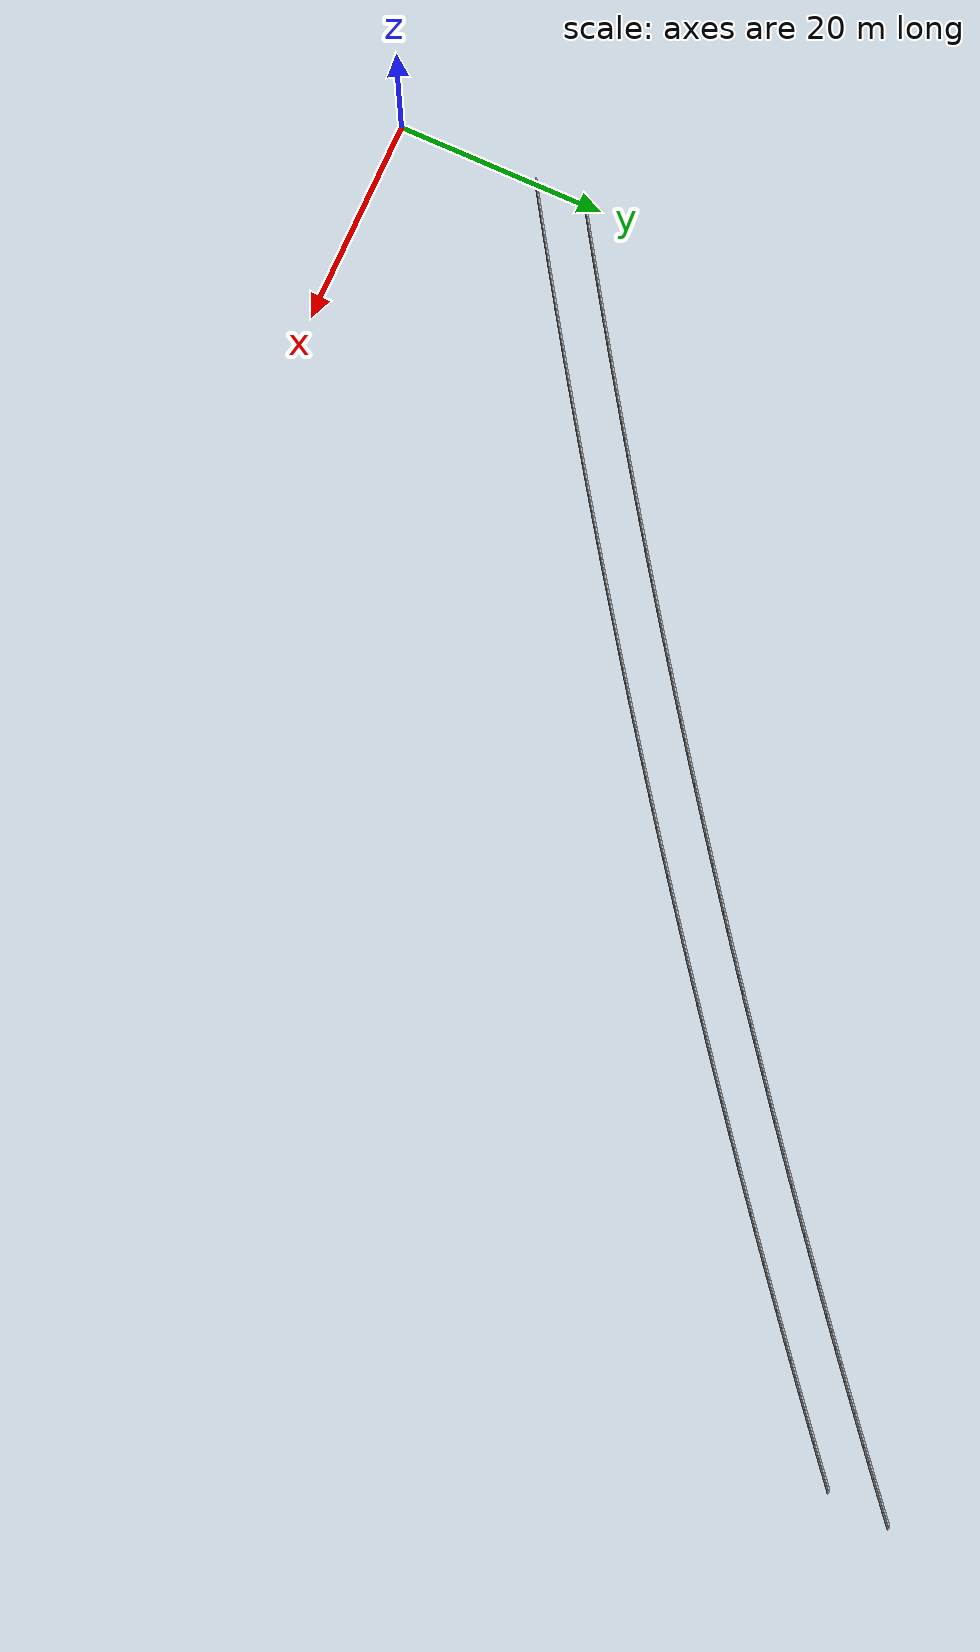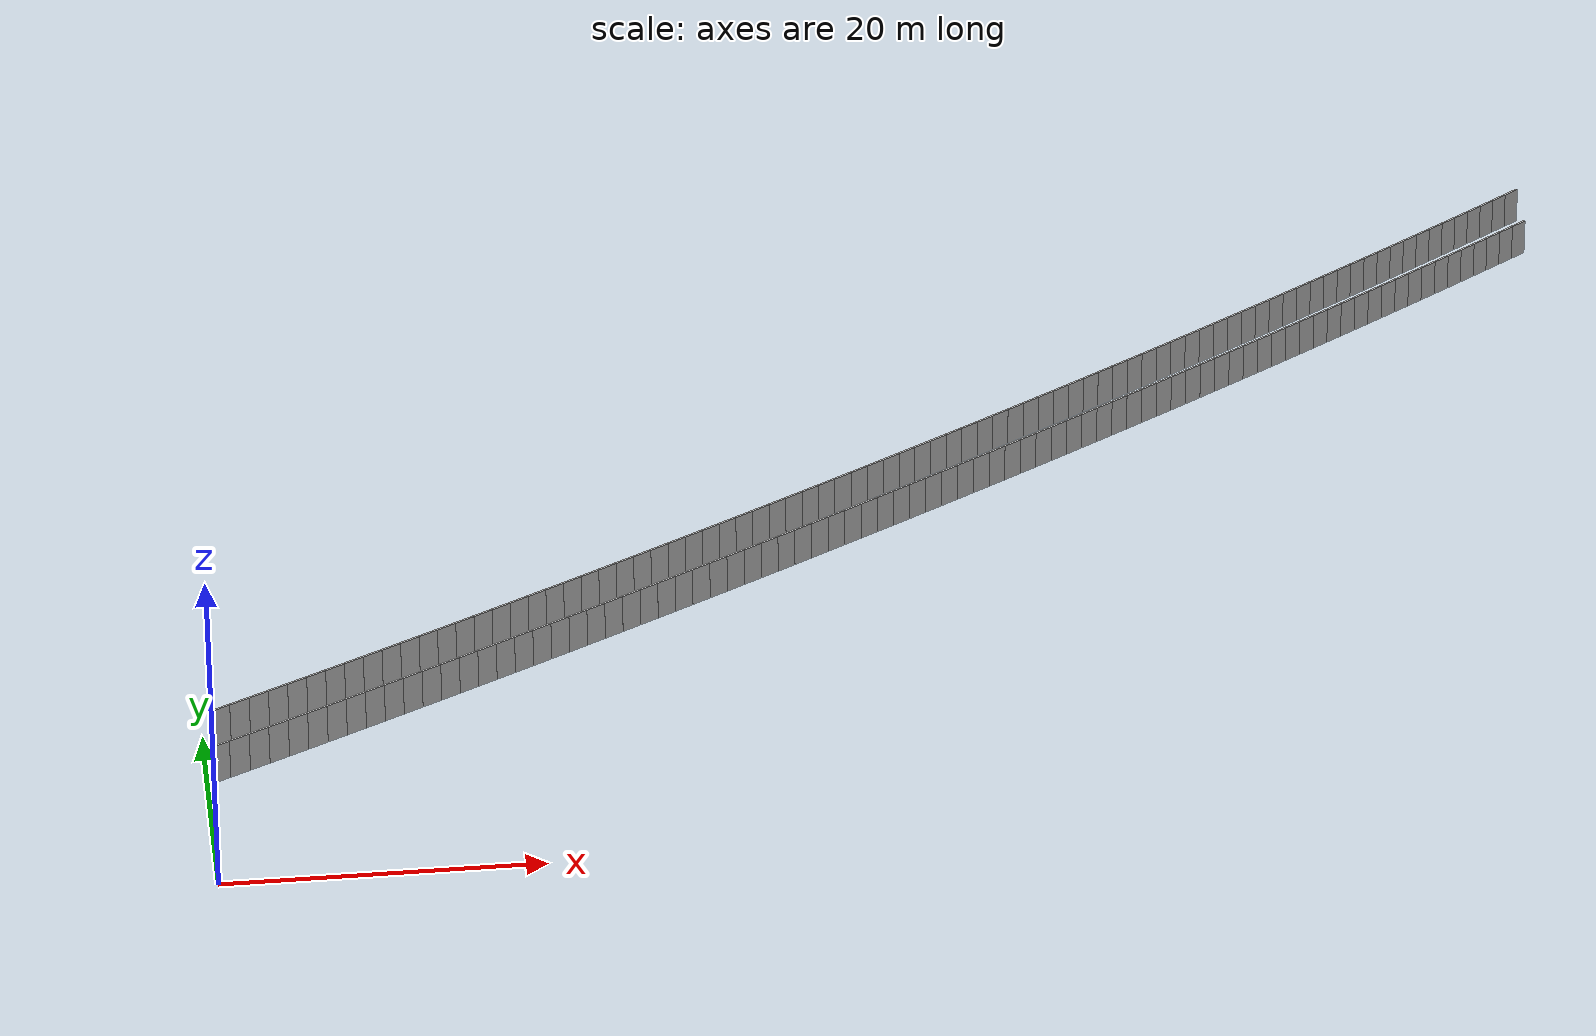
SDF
<?xml version="1.0" ?>
<sdf version="1.6">
  <model name="sps_1803">
    <pose frame="">0 0 0 0 -0 0</pose>
    <static>1</static>
    <self_collide>0</self_collide>
    <allow_auto_disable>0</allow_auto_disable>
    <link name="Wall4065">
      <kinematic>0</kinematic>
      <gravity>1</gravity>
      <self_collide>0</self_collide>
      <collision name="collision">
        <geometry>
          <box>
            <size>1.49655 0.15 2.5</size>
          </box>
        </geometry>
        <pose frame="">0 0 0 0 -0 0</pose>
      </collision>
      <visual name="visual">
        <geometry>
          <box>
            <size>1.49655 0.15 2.5</size>
          </box>
        </geometry>
        <pose frame="">0 0 0 0 -0 0</pose>
        <cast_shadows>1</cast_shadows>
        <transparency>0.0</transparency>
      </visual>
      <pose frame="">1.08144 19.0442 1.25 0 -0 0.571431</pose>
    </link>
    <link name="Wall4066">
      <kinematic>0</kinematic>
      <gravity>1</gravity>
      <self_collide>0</self_collide>
      <collision name="collision">
        <geometry>
          <box>
            <size>1.49672 0.15 2.5</size>
          </box>
        </geometry>
        <pose frame="">0 0 0 0 -0 0</pose>
      </collision>
      <visual name="visual">
        <geometry>
          <box>
            <size>1.49672 0.15 2.5</size>
          </box>
        </geometry>
        <pose frame="">0 0 0 0 -0 0</pose>
        <cast_shadows>1</cast_shadows>
        <transparency>0.0</transparency>
      </visual>
      <pose frame="">2.33974 19.8545 1.25 0 -0 0.572812</pose>
    </link>
    <link name="Wall4067">
      <kinematic>0</kinematic>
      <gravity>1</gravity>
      <self_collide>0</self_collide>
      <collision name="collision">
        <geometry>
          <box>
            <size>1.49635 0.15 2.5</size>
          </box>
        </geometry>
        <pose frame="">0 0 0 0 -0 0</pose>
      </collision>
      <visual name="visual">
        <geometry>
          <box>
            <size>1.49635 0.15 2.5</size>
          </box>
        </geometry>
        <pose frame="">0 0 0 0 -0 0</pose>
        <cast_shadows>1</cast_shadows>
        <transparency>0.0</transparency>
      </visual>
      <pose frame="">3.59676 20.6666 1.25 0 -0 0.574381</pose>
    </link>
    <link name="Wall4068">
      <kinematic>0</kinematic>
      <gravity>1</gravity>
      <self_collide>0</self_collide>
      <collision name="collision">
        <geometry>
          <box>
            <size>1.49665 0.15 2.5</size>
          </box>
        </geometry>
        <pose frame="">0 0 0 0 -0 0</pose>
      </collision>
      <visual name="visual">
        <geometry>
          <box>
            <size>1.49665 0.15 2.5</size>
          </box>
        </geometry>
        <pose frame="">0 0 0 0 -0 0</pose>
        <cast_shadows>1</cast_shadows>
        <transparency>0.0</transparency>
      </visual>
      <pose frame="">4.85238 21.4808 1.25 0 -0 0.576194</pose>
    </link>
    <link name="Wall4069">
      <kinematic>0</kinematic>
      <gravity>1</gravity>
      <self_collide>0</self_collide>
      <collision name="collision">
        <geometry>
          <box>
            <size>1.49649 0.15 2.5</size>
          </box>
        </geometry>
        <pose frame="">0 0 0 0 -0 0</pose>
      </collision>
      <visual name="visual">
        <geometry>
          <box>
            <size>1.49649 0.15 2.5</size>
          </box>
        </geometry>
        <pose frame="">0 0 0 0 -0 0</pose>
        <cast_shadows>1</cast_shadows>
        <transparency>0.0</transparency>
      </visual>
      <pose frame="">6.10677 22.297 1.25 0 -0 0.577528</pose>
    </link>
    <link name="Wall4070">
      <kinematic>0</kinematic>
      <gravity>1</gravity>
      <self_collide>0</self_collide>
      <collision name="collision">
        <geometry>
          <box>
            <size>1.49649 0.15 2.5</size>
          </box>
        </geometry>
        <pose frame="">0 0 0 0 -0 0</pose>
      </collision>
      <visual name="visual">
        <geometry>
          <box>
            <size>1.49649 0.15 2.5</size>
          </box>
        </geometry>
        <pose frame="">0 0 0 0 -0 0</pose>
        <cast_shadows>1</cast_shadows>
        <transparency>0.0</transparency>
      </visual>
      <pose frame="">7.35985 23.1151 1.25 0 -0 0.579236</pose>
    </link>
    <link name="Wall4071">
      <kinematic>0</kinematic>
      <gravity>1</gravity>
      <self_collide>0</self_collide>
      <collision name="collision">
        <geometry>
          <box>
            <size>1.49665 0.15 2.5</size>
          </box>
        </geometry>
        <pose frame="">0 0 0 0 -0 0</pose>
      </collision>
      <visual name="visual">
        <geometry>
          <box>
            <size>1.49665 0.15 2.5</size>
          </box>
        </geometry>
        <pose frame="">0 0 0 0 -0 0</pose>
        <cast_shadows>1</cast_shadows>
        <transparency>0.0</transparency>
      </visual>
      <pose frame="">8.61166 23.9353 1.25 0 -0 0.58082</pose>
    </link>
    <link name="Wall4072">
      <kinematic>0</kinematic>
      <gravity>1</gravity>
      <self_collide>0</self_collide>
      <collision name="collision">
        <geometry>
          <box>
            <size>1.49655 0.15 2.5</size>
          </box>
        </geometry>
        <pose frame="">0 0 0 0 -0 0</pose>
      </collision>
      <visual name="visual">
        <geometry>
          <box>
            <size>1.49655 0.15 2.5</size>
          </box>
        </geometry>
        <pose frame="">0 0 0 0 -0 0</pose>
        <cast_shadows>1</cast_shadows>
        <transparency>0.0</transparency>
      </visual>
      <pose frame="">9.86217 24.7575 1.25 0 -0 0.582426</pose>
    </link>
    <link name="Wall4073">
      <kinematic>0</kinematic>
      <gravity>1</gravity>
      <self_collide>0</self_collide>
      <collision name="collision">
        <geometry>
          <box>
            <size>1.49654 0.15 2.5</size>
          </box>
        </geometry>
        <pose frame="">0 0 0 0 -0 0</pose>
      </collision>
      <visual name="visual">
        <geometry>
          <box>
            <size>1.49654 0.15 2.5</size>
          </box>
        </geometry>
        <pose frame="">0 0 0 0 -0 0</pose>
        <cast_shadows>1</cast_shadows>
        <transparency>0.0</transparency>
      </visual>
      <pose frame="">11.1114 25.5816 1.25 0 -0 0.583897</pose>
    </link>
    <link name="Wall4074">
      <kinematic>0</kinematic>
      <gravity>1</gravity>
      <self_collide>0</self_collide>
      <collision name="collision">
        <geometry>
          <box>
            <size>1.49648 0.15 2.5</size>
          </box>
        </geometry>
        <pose frame="">0 0 0 0 -0 0</pose>
      </collision>
      <visual name="visual">
        <geometry>
          <box>
            <size>1.49648 0.15 2.5</size>
          </box>
        </geometry>
        <pose frame="">0 0 0 0 -0 0</pose>
        <cast_shadows>1</cast_shadows>
        <transparency>0.0</transparency>
      </visual>
      <pose frame="">12.3593 26.4076 1.25 0 -0 0.585537</pose>
    </link>
    <link name="Wall4075">
      <kinematic>0</kinematic>
      <gravity>1</gravity>
      <self_collide>0</self_collide>
      <collision name="collision">
        <geometry>
          <box>
            <size>1.49639 0.15 2.5</size>
          </box>
        </geometry>
        <pose frame="">0 0 0 0 -0 0</pose>
      </collision>
      <visual name="visual">
        <geometry>
          <box>
            <size>1.49639 0.15 2.5</size>
          </box>
        </geometry>
        <pose frame="">0 0 0 0 -0 0</pose>
        <cast_shadows>1</cast_shadows>
        <transparency>0.0</transparency>
      </visual>
      <pose frame="">13.6058 27.2356 1.25 0 -0 0.587143</pose>
    </link>
    <link name="Wall4076">
      <kinematic>0</kinematic>
      <gravity>1</gravity>
      <self_collide>0</self_collide>
      <collision name="collision">
        <geometry>
          <box>
            <size>1.4965 0.15 2.5</size>
          </box>
        </geometry>
        <pose frame="">0 0 0 0 -0 0</pose>
      </collision>
      <visual name="visual">
        <geometry>
          <box>
            <size>1.4965 0.15 2.5</size>
          </box>
        </geometry>
        <pose frame="">0 0 0 0 -0 0</pose>
        <cast_shadows>1</cast_shadows>
        <transparency>0.0</transparency>
      </visual>
      <pose frame="">14.8509 28.0656 1.25 0 -0 0.588715</pose>
    </link>
    <link name="Wall4077">
      <kinematic>0</kinematic>
      <gravity>1</gravity>
      <self_collide>0</self_collide>
      <collision name="collision">
        <geometry>
          <box>
            <size>1.4966 0.15 2.5</size>
          </box>
        </geometry>
        <pose frame="">0 0 0 0 -0 0</pose>
      </collision>
      <visual name="visual">
        <geometry>
          <box>
            <size>1.4966 0.15 2.5</size>
          </box>
        </geometry>
        <pose frame="">0 0 0 0 -0 0</pose>
        <cast_shadows>1</cast_shadows>
        <transparency>0.0</transparency>
      </visual>
      <pose frame="">16.0948 28.8977 1.25 0 -0 0.590434</pose>
    </link>
    <link name="Wall4078">
      <kinematic>0</kinematic>
      <gravity>1</gravity>
      <self_collide>0</self_collide>
      <collision name="collision">
        <geometry>
          <box>
            <size>1.49651 0.15 2.5</size>
          </box>
        </geometry>
        <pose frame="">0 0 0 0 -0 0</pose>
      </collision>
      <visual name="visual">
        <geometry>
          <box>
            <size>1.49651 0.15 2.5</size>
          </box>
        </geometry>
        <pose frame="">0 0 0 0 -0 0</pose>
        <cast_shadows>1</cast_shadows>
        <transparency>0.0</transparency>
      </visual>
      <pose frame="">17.3375 29.7317 1.25 0 -0 0.591803</pose>
    </link>
    <link name="Wall4079">
      <kinematic>0</kinematic>
      <gravity>1</gravity>
      <self_collide>0</self_collide>
      <collision name="collision">
        <geometry>
          <box>
            <size>1.49654 0.15 2.5</size>
          </box>
        </geometry>
        <pose frame="">0 0 0 0 -0 0</pose>
      </collision>
      <visual name="visual">
        <geometry>
          <box>
            <size>1.49654 0.15 2.5</size>
          </box>
        </geometry>
        <pose frame="">0 0 0 0 -0 0</pose>
        <cast_shadows>1</cast_shadows>
        <transparency>0.0</transparency>
      </visual>
      <pose frame="">18.5788 30.5676 1.25 0 -0 0.593511</pose>
    </link>
    <link name="Wall4080">
      <kinematic>0</kinematic>
      <gravity>1</gravity>
      <self_collide>0</self_collide>
      <collision name="collision">
        <geometry>
          <box>
            <size>1.49665 0.15 2.5</size>
          </box>
        </geometry>
        <pose frame="">0 0 0 0 -0 0</pose>
      </collision>
      <visual name="visual">
        <geometry>
          <box>
            <size>1.49665 0.15 2.5</size>
          </box>
        </geometry>
        <pose frame="">0 0 0 0 -0 0</pose>
        <cast_shadows>1</cast_shadows>
        <transparency>0.0</transparency>
      </visual>
      <pose frame="">19.8187 31.4056 1.25 0 -0 0.595083</pose>
    </link>
    <link name="Wall4081">
      <kinematic>0</kinematic>
      <gravity>1</gravity>
      <self_collide>0</self_collide>
      <collision name="collision">
        <geometry>
          <box>
            <size>1.49637 0.15 2.5</size>
          </box>
        </geometry>
        <pose frame="">0 0 0 0 -0 0</pose>
      </collision>
      <visual name="visual">
        <geometry>
          <box>
            <size>1.49637 0.15 2.5</size>
          </box>
        </geometry>
        <pose frame="">0 0 0 0 -0 0</pose>
        <cast_shadows>1</cast_shadows>
        <transparency>0.0</transparency>
      </visual>
      <pose frame="">21.0573 32.2455 1.25 0 -0 0.596691</pose>
    </link>
    <link name="Wall4082">
      <kinematic>0</kinematic>
      <gravity>1</gravity>
      <self_collide>0</self_collide>
      <collision name="collision">
        <geometry>
          <box>
            <size>1.49666 0.15 2.5</size>
          </box>
        </geometry>
        <pose frame="">0 0 0 0 -0 0</pose>
      </collision>
      <visual name="visual">
        <geometry>
          <box>
            <size>1.49666 0.15 2.5</size>
          </box>
        </geometry>
        <pose frame="">0 0 0 0 -0 0</pose>
        <cast_shadows>1</cast_shadows>
        <transparency>0.0</transparency>
      </visual>
      <pose frame="">22.2946 33.0873 1.25 0 -0 0.598137</pose>
    </link>
    <link name="Wall4083">
      <kinematic>0</kinematic>
      <gravity>1</gravity>
      <self_collide>0</self_collide>
      <collision name="collision">
        <geometry>
          <box>
            <size>1.49648 0.15 2.5</size>
          </box>
        </geometry>
        <pose frame="">0 0 0 0 -0 0</pose>
      </collision>
      <visual name="visual">
        <geometry>
          <box>
            <size>1.49648 0.15 2.5</size>
          </box>
        </geometry>
        <pose frame="">0 0 0 0 -0 0</pose>
        <cast_shadows>1</cast_shadows>
        <transparency>0.0</transparency>
      </visual>
      <pose frame="">23.5307 33.9311 1.25 0 -0 0.599846</pose>
    </link>
    <link name="Wall4084">
      <kinematic>0</kinematic>
      <gravity>1</gravity>
      <self_collide>0</self_collide>
      <collision name="collision">
        <geometry>
          <box>
            <size>1.49651 0.15 2.5</size>
          </box>
        </geometry>
        <pose frame="">0 0 0 0 -0 0</pose>
      </collision>
      <visual name="visual">
        <geometry>
          <box>
            <size>1.49651 0.15 2.5</size>
          </box>
        </geometry>
        <pose frame="">0 0 0 0 -0 0</pose>
        <cast_shadows>1</cast_shadows>
        <transparency>0.0</transparency>
      </visual>
      <pose frame="">24.7653 34.7768 1.25 0 -0 0.601317</pose>
    </link>
    <link name="Wall4085">
      <kinematic>0</kinematic>
      <gravity>1</gravity>
      <self_collide>0</self_collide>
      <collision name="collision">
        <geometry>
          <box>
            <size>1.49655 0.15 2.5</size>
          </box>
        </geometry>
        <pose frame="">0 0 0 0 -0 0</pose>
      </collision>
      <visual name="visual">
        <geometry>
          <box>
            <size>1.49655 0.15 2.5</size>
          </box>
        </geometry>
        <pose frame="">0 0 0 0 -0 0</pose>
        <cast_shadows>1</cast_shadows>
        <transparency>0.0</transparency>
      </visual>
      <pose frame="">25.9986 35.6245 1.25 0 -0 0.603081</pose>
    </link>
    <link name="Wall4086">
      <kinematic>0</kinematic>
      <gravity>1</gravity>
      <self_collide>0</self_collide>
      <collision name="collision">
        <geometry>
          <box>
            <size>1.49645 0.15 2.5</size>
          </box>
        </geometry>
        <pose frame="">0 0 0 0 -0 0</pose>
      </collision>
      <visual name="visual">
        <geometry>
          <box>
            <size>1.49645 0.15 2.5</size>
          </box>
        </geometry>
        <pose frame="">0 0 0 0 -0 0</pose>
        <cast_shadows>1</cast_shadows>
        <transparency>0.0</transparency>
      </visual>
      <pose frame="">27.2304 36.4742 1.25 0 -0 0.604564</pose>
    </link>
    <link name="Wall4087">
      <kinematic>0</kinematic>
      <gravity>1</gravity>
      <self_collide>0</self_collide>
      <collision name="collision">
        <geometry>
          <box>
            <size>1.49664 0.15 2.5</size>
          </box>
        </geometry>
        <pose frame="">0 0 0 0 -0 0</pose>
      </collision>
      <visual name="visual">
        <geometry>
          <box>
            <size>1.49664 0.15 2.5</size>
          </box>
        </geometry>
        <pose frame="">0 0 0 0 -0 0</pose>
        <cast_shadows>1</cast_shadows>
        <transparency>0.0</transparency>
      </visual>
      <pose frame="">28.4611 37.3258 1.25 0 -0 0.606112</pose>
    </link>
    <link name="Wall4088">
      <kinematic>0</kinematic>
      <gravity>1</gravity>
      <self_collide>0</self_collide>
      <collision name="collision">
        <geometry>
          <box>
            <size>1.49658 0.15 2.5</size>
          </box>
        </geometry>
        <pose frame="">0 0 0 0 -0 0</pose>
      </collision>
      <visual name="visual">
        <geometry>
          <box>
            <size>1.49658 0.15 2.5</size>
          </box>
        </geometry>
        <pose frame="">0 0 0 0 -0 0</pose>
        <cast_shadows>1</cast_shadows>
        <transparency>0.0</transparency>
      </visual>
      <pose frame="">29.6904 38.1794 1.25 0 -0 0.607776</pose>
    </link>
    <link name="Wall4089">
      <kinematic>0</kinematic>
      <gravity>1</gravity>
      <self_collide>0</self_collide>
      <collision name="collision">
        <geometry>
          <box>
            <size>1.4966 0.15 2.5</size>
          </box>
        </geometry>
        <pose frame="">0 0 0 0 -0 0</pose>
      </collision>
      <visual name="visual">
        <geometry>
          <box>
            <size>1.4966 0.15 2.5</size>
          </box>
        </geometry>
        <pose frame="">0 0 0 0 -0 0</pose>
        <cast_shadows>1</cast_shadows>
        <transparency>0.0</transparency>
      </visual>
      <pose frame="">30.9183 39.035 1.25 0 -0 0.609359</pose>
    </link>
    <link name="Wall4090">
      <kinematic>0</kinematic>
      <gravity>1</gravity>
      <self_collide>0</self_collide>
      <collision name="collision">
        <geometry>
          <box>
            <size>1.4966 0.15 2.5</size>
          </box>
        </geometry>
        <pose frame="">0 0 0 0 -0 0</pose>
      </collision>
      <visual name="visual">
        <geometry>
          <box>
            <size>1.4966 0.15 2.5</size>
          </box>
        </geometry>
        <pose frame="">0 0 0 0 -0 0</pose>
        <cast_shadows>1</cast_shadows>
        <transparency>0.0</transparency>
      </visual>
      <pose frame="">32.1449 39.8925 1.25 0 -0 0.610853</pose>
    </link>
    <link name="Wall4091">
      <kinematic>0</kinematic>
      <gravity>1</gravity>
      <self_collide>0</self_collide>
      <collision name="collision">
        <geometry>
          <box>
            <size>1.49651 0.15 2.5</size>
          </box>
        </geometry>
        <pose frame="">0 0 0 0 -0 0</pose>
      </collision>
      <visual name="visual">
        <geometry>
          <box>
            <size>1.49651 0.15 2.5</size>
          </box>
        </geometry>
        <pose frame="">0 0 0 0 -0 0</pose>
        <cast_shadows>1</cast_shadows>
        <transparency>0.0</transparency>
      </visual>
      <pose frame="">33.37 40.7519 1.25 0 -0 0.61254</pose>
    </link>
    <link name="Wall4092">
      <kinematic>0</kinematic>
      <gravity>1</gravity>
      <self_collide>0</self_collide>
      <collision name="collision">
        <geometry>
          <box>
            <size>1.49638 0.15 2.5</size>
          </box>
        </geometry>
        <pose frame="">0 0 0 0 -0 0</pose>
      </collision>
      <visual name="visual">
        <geometry>
          <box>
            <size>1.49638 0.15 2.5</size>
          </box>
        </geometry>
        <pose frame="">0 0 0 0 -0 0</pose>
        <cast_shadows>1</cast_shadows>
        <transparency>0.0</transparency>
      </visual>
      <pose frame="">34.5938 41.6132 1.25 0 -0 0.614047</pose>
    </link>
    <link name="Wall4093">
      <kinematic>0</kinematic>
      <gravity>1</gravity>
      <self_collide>0</self_collide>
      <collision name="collision">
        <geometry>
          <box>
            <size>1.49658 0.15 2.5</size>
          </box>
        </geometry>
        <pose frame="">0 0 0 0 -0 0</pose>
      </collision>
      <visual name="visual">
        <geometry>
          <box>
            <size>1.49658 0.15 2.5</size>
          </box>
        </geometry>
        <pose frame="">0 0 0 0 -0 0</pose>
        <cast_shadows>1</cast_shadows>
        <transparency>0.0</transparency>
      </visual>
      <pose frame="">35.8162 42.4764 1.25 0 -0 0.615651</pose>
    </link>
    <link name="Wall4094">
      <kinematic>0</kinematic>
      <gravity>1</gravity>
      <self_collide>0</self_collide>
      <collision name="collision">
        <geometry>
          <box>
            <size>1.49652 0.15 2.5</size>
          </box>
        </geometry>
        <pose frame="">0 0 0 0 -0 0</pose>
      </collision>
      <visual name="visual">
        <geometry>
          <box>
            <size>1.49652 0.15 2.5</size>
          </box>
        </geometry>
        <pose frame="">0 0 0 0 -0 0</pose>
        <cast_shadows>1</cast_shadows>
        <transparency>0.0</transparency>
      </visual>
      <pose frame="">37.0373 43.3416 1.25 0 -0 0.617225</pose>
    </link>
    <link name="Wall4095">
      <kinematic>0</kinematic>
      <gravity>1</gravity>
      <self_collide>0</self_collide>
      <collision name="collision">
        <geometry>
          <box>
            <size>1.49673 0.15 2.5</size>
          </box>
        </geometry>
        <pose frame="">0 0 0 0 -0 0</pose>
      </collision>
      <visual name="visual">
        <geometry>
          <box>
            <size>1.49673 0.15 2.5</size>
          </box>
        </geometry>
        <pose frame="">0 0 0 0 -0 0</pose>
        <cast_shadows>1</cast_shadows>
        <transparency>0.0</transparency>
      </visual>
      <pose frame="">38.2571 44.2088 1.25 0 -0 0.618827</pose>
    </link>
    <link name="Wall4096">
      <kinematic>0</kinematic>
      <gravity>1</gravity>
      <self_collide>0</self_collide>
      <collision name="collision">
        <geometry>
          <box>
            <size>1.49647 0.15 2.5</size>
          </box>
        </geometry>
        <pose frame="">0 0 0 0 -0 0</pose>
      </collision>
      <visual name="visual">
        <geometry>
          <box>
            <size>1.49647 0.15 2.5</size>
          </box>
        </geometry>
        <pose frame="">0 0 0 0 -0 0</pose>
        <cast_shadows>1</cast_shadows>
        <transparency>0.0</transparency>
      </visual>
      <pose frame="">39.4755 45.0779 1.25 0 -0 0.620406</pose>
    </link>
    <link name="Wall4097">
      <kinematic>0</kinematic>
      <gravity>1</gravity>
      <self_collide>0</self_collide>
      <collision name="collision">
        <geometry>
          <box>
            <size>1.49639 0.15 2.5</size>
          </box>
        </geometry>
        <pose frame="">0 0 0 0 -0 0</pose>
      </collision>
      <visual name="visual">
        <geometry>
          <box>
            <size>1.49639 0.15 2.5</size>
          </box>
        </geometry>
        <pose frame="">0 0 0 0 -0 0</pose>
        <cast_shadows>1</cast_shadows>
        <transparency>0.0</transparency>
      </visual>
      <pose frame="">40.6923 45.9488 1.25 0 -0 0.621947</pose>
    </link>
    <link name="Wall4098">
      <kinematic>0</kinematic>
      <gravity>1</gravity>
      <self_collide>0</self_collide>
      <collision name="collision">
        <geometry>
          <box>
            <size>1.4967 0.15 2.5</size>
          </box>
        </geometry>
        <pose frame="">0 0 0 0 -0 0</pose>
      </collision>
      <visual name="visual">
        <geometry>
          <box>
            <size>1.4967 0.15 2.5</size>
          </box>
        </geometry>
        <pose frame="">0 0 0 0 -0 0</pose>
        <cast_shadows>1</cast_shadows>
        <transparency>0.0</transparency>
      </visual>
      <pose frame="">41.908 46.8217 1.25 0 -0 0.623558</pose>
    </link>
    <link name="Wall4099">
      <kinematic>0</kinematic>
      <gravity>1</gravity>
      <self_collide>0</self_collide>
      <collision name="collision">
        <geometry>
          <box>
            <size>1.49643 0.15 2.5</size>
          </box>
        </geometry>
        <pose frame="">0 0 0 0 -0 0</pose>
      </collision>
      <visual name="visual">
        <geometry>
          <box>
            <size>1.49643 0.15 2.5</size>
          </box>
        </geometry>
        <pose frame="">0 0 0 0 -0 0</pose>
        <cast_shadows>1</cast_shadows>
        <transparency>0.0</transparency>
      </visual>
      <pose frame="">43.1222 47.6966 1.25 0 -0 0.625195</pose>
    </link>
    <link name="Wall4100">
      <kinematic>0</kinematic>
      <gravity>1</gravity>
      <self_collide>0</self_collide>
      <collision name="collision">
        <geometry>
          <box>
            <size>1.49652 0.15 2.5</size>
          </box>
        </geometry>
        <pose frame="">0 0 0 0 -0 0</pose>
      </collision>
      <visual name="visual">
        <geometry>
          <box>
            <size>1.49652 0.15 2.5</size>
          </box>
        </geometry>
        <pose frame="">0 0 0 0 -0 0</pose>
        <cast_shadows>1</cast_shadows>
        <transparency>0.0</transparency>
      </visual>
      <pose frame="">44.3349 48.5734 1.25 0 -0 0.626811</pose>
    </link>
    <link name="Wall4101">
      <kinematic>0</kinematic>
      <gravity>1</gravity>
      <self_collide>0</self_collide>
      <collision name="collision">
        <geometry>
          <box>
            <size>1.49656 0.15 2.5</size>
          </box>
        </geometry>
        <pose frame="">0 0 0 0 -0 0</pose>
      </collision>
      <visual name="visual">
        <geometry>
          <box>
            <size>1.49656 0.15 2.5</size>
          </box>
        </geometry>
        <pose frame="">0 0 0 0 -0 0</pose>
        <cast_shadows>1</cast_shadows>
        <transparency>0.0</transparency>
      </visual>
      <pose frame="">45.5463 49.4521 1.25 0 -0 0.628305</pose>
    </link>
    <link name="Wall4102">
      <kinematic>0</kinematic>
      <gravity>1</gravity>
      <self_collide>0</self_collide>
      <collision name="collision">
        <geometry>
          <box>
            <size>1.49633 0.15 2.5</size>
          </box>
        </geometry>
        <pose frame="">0 0 0 0 -0 0</pose>
      </collision>
      <visual name="visual">
        <geometry>
          <box>
            <size>1.49633 0.15 2.5</size>
          </box>
        </geometry>
        <pose frame="">0 0 0 0 -0 0</pose>
        <cast_shadows>1</cast_shadows>
        <transparency>0.0</transparency>
      </visual>
      <pose frame="">46.7562 50.3326 1.25 0 -0 0.629828</pose>
    </link>
    <link name="Wall4103">
      <kinematic>0</kinematic>
      <gravity>1</gravity>
      <self_collide>0</self_collide>
      <collision name="collision">
        <geometry>
          <box>
            <size>1.49668 0.15 2.5</size>
          </box>
        </geometry>
        <pose frame="">0 0 0 0 -0 0</pose>
      </collision>
      <visual name="visual">
        <geometry>
          <box>
            <size>1.49668 0.15 2.5</size>
          </box>
        </geometry>
        <pose frame="">0 0 0 0 -0 0</pose>
        <cast_shadows>1</cast_shadows>
        <transparency>0.0</transparency>
      </visual>
      <pose frame="">47.9649 51.2151 1.25 0 -0 0.631528</pose>
    </link>
    <link name="Wall4104">
      <kinematic>0</kinematic>
      <gravity>1</gravity>
      <self_collide>0</self_collide>
      <collision name="collision">
        <geometry>
          <box>
            <size>1.49663 0.15 2.5</size>
          </box>
        </geometry>
        <pose frame="">0 0 0 0 -0 0</pose>
      </collision>
      <visual name="visual">
        <geometry>
          <box>
            <size>1.49663 0.15 2.5</size>
          </box>
        </geometry>
        <pose frame="">0 0 0 0 -0 0</pose>
        <cast_shadows>1</cast_shadows>
        <transparency>0.0</transparency>
      </visual>
      <pose frame="">49.1722 52.0996 1.25 0 -0 0.633069</pose>
    </link>
    <link name="Wall4105">
      <kinematic>0</kinematic>
      <gravity>1</gravity>
      <self_collide>0</self_collide>
      <collision name="collision">
        <geometry>
          <box>
            <size>1.49635 0.15 2.5</size>
          </box>
        </geometry>
        <pose frame="">0 0 0 0 -0 0</pose>
      </collision>
      <visual name="visual">
        <geometry>
          <box>
            <size>1.49635 0.15 2.5</size>
          </box>
        </geometry>
        <pose frame="">0 0 0 0 -0 0</pose>
        <cast_shadows>1</cast_shadows>
        <transparency>0.0</transparency>
      </visual>
      <pose frame="">50.378 52.9859 1.25 0 -0 0.634674</pose>
    </link>
    <link name="Wall4106">
      <kinematic>0</kinematic>
      <gravity>1</gravity>
      <self_collide>0</self_collide>
      <collision name="collision">
        <geometry>
          <box>
            <size>1.49643 0.15 2.5</size>
          </box>
        </geometry>
        <pose frame="">0 0 0 0 -0 0</pose>
      </collision>
      <visual name="visual">
        <geometry>
          <box>
            <size>1.49643 0.15 2.5</size>
          </box>
        </geometry>
        <pose frame="">0 0 0 0 -0 0</pose>
        <cast_shadows>1</cast_shadows>
        <transparency>0.0</transparency>
      </visual>
      <pose frame="">51.5822 53.8741 1.25 0 -0 0.636257</pose>
    </link>
    <link name="Wall4107">
      <kinematic>0</kinematic>
      <gravity>1</gravity>
      <self_collide>0</self_collide>
      <collision name="collision">
        <geometry>
          <box>
            <size>1.49668 0.15 2.5</size>
          </box>
        </geometry>
        <pose frame="">0 0 0 0 -0 0</pose>
      </collision>
      <visual name="visual">
        <geometry>
          <box>
            <size>1.49668 0.15 2.5</size>
          </box>
        </geometry>
        <pose frame="">0 0 0 0 -0 0</pose>
        <cast_shadows>1</cast_shadows>
        <transparency>0.0</transparency>
      </visual>
      <pose frame="">52.7852 54.7643 1.25 0 -0 0.637857</pose>
    </link>
    <link name="Wall4108">
      <kinematic>0</kinematic>
      <gravity>1</gravity>
      <self_collide>0</self_collide>
      <collision name="collision">
        <geometry>
          <box>
            <size>1.49646 0.15 2.5</size>
          </box>
        </geometry>
        <pose frame="">0 0 0 0 -0 0</pose>
      </collision>
      <visual name="visual">
        <geometry>
          <box>
            <size>1.49646 0.15 2.5</size>
          </box>
        </geometry>
        <pose frame="">0 0 0 0 -0 0</pose>
        <cast_shadows>1</cast_shadows>
        <transparency>0.0</transparency>
      </visual>
      <pose frame="">53.9868 55.6564 1.25 0 -0 0.639439</pose>
    </link>
    <link name="Wall4109">
      <kinematic>0</kinematic>
      <gravity>1</gravity>
      <self_collide>0</self_collide>
      <collision name="collision">
        <geometry>
          <box>
            <size>1.49665 0.15 2.5</size>
          </box>
        </geometry>
        <pose frame="">0 0 0 0 -0 0</pose>
      </collision>
      <visual name="visual">
        <geometry>
          <box>
            <size>1.49665 0.15 2.5</size>
          </box>
        </geometry>
        <pose frame="">0 0 0 0 -0 0</pose>
        <cast_shadows>1</cast_shadows>
        <transparency>0.0</transparency>
      </visual>
      <pose frame="">55.187 56.5504 1.25 0 -0 0.640973</pose>
    </link>
    <link name="Wall4110">
      <kinematic>0</kinematic>
      <gravity>1</gravity>
      <self_collide>0</self_collide>
      <collision name="collision">
        <geometry>
          <box>
            <size>1.49667 0.15 2.5</size>
          </box>
        </geometry>
        <pose frame="">0 0 0 0 -0 0</pose>
      </collision>
      <visual name="visual">
        <geometry>
          <box>
            <size>1.49667 0.15 2.5</size>
          </box>
        </geometry>
        <pose frame="">0 0 0 0 -0 0</pose>
        <cast_shadows>1</cast_shadows>
        <transparency>0.0</transparency>
      </visual>
      <pose frame="">56.3859 57.4463 1.25 0 -0 0.64249</pose>
    </link>
    <link name="Wall4111">
      <kinematic>0</kinematic>
      <gravity>1</gravity>
      <self_collide>0</self_collide>
      <collision name="collision">
        <geometry>
          <box>
            <size>1.49656 0.15 2.5</size>
          </box>
        </geometry>
        <pose frame="">0 0 0 0 -0 0</pose>
      </collision>
      <visual name="visual">
        <geometry>
          <box>
            <size>1.49656 0.15 2.5</size>
          </box>
        </geometry>
        <pose frame="">0 0 0 0 -0 0</pose>
        <cast_shadows>1</cast_shadows>
        <transparency>0.0</transparency>
      </visual>
      <pose frame="">57.5834 58.3441 1.25 0 -0 0.644227</pose>
    </link>
    <link name="Wall4112">
      <kinematic>0</kinematic>
      <gravity>1</gravity>
      <self_collide>0</self_collide>
      <collision name="collision">
        <geometry>
          <box>
            <size>1.4965 0.15 2.5</size>
          </box>
        </geometry>
        <pose frame="">0 0 0 0 -0 0</pose>
      </collision>
      <visual name="visual">
        <geometry>
          <box>
            <size>1.4965 0.15 2.5</size>
          </box>
        </geometry>
        <pose frame="">0 0 0 0 -0 0</pose>
        <cast_shadows>1</cast_shadows>
        <transparency>0.0</transparency>
      </visual>
      <pose frame="">58.7792 59.2439 1.25 0 -0 0.64594</pose>
    </link>
    <link name="Wall4113">
      <kinematic>0</kinematic>
      <gravity>1</gravity>
      <self_collide>0</self_collide>
      <collision name="collision">
        <geometry>
          <box>
            <size>1.49648 0.15 2.5</size>
          </box>
        </geometry>
        <pose frame="">0 0 0 0 -0 0</pose>
      </collision>
      <visual name="visual">
        <geometry>
          <box>
            <size>1.49648 0.15 2.5</size>
          </box>
        </geometry>
        <pose frame="">0 0 0 0 -0 0</pose>
        <cast_shadows>1</cast_shadows>
        <transparency>0.0</transparency>
      </visual>
      <pose frame="">59.9736 60.1455 1.25 0 -0 0.647278</pose>
    </link>
    <link name="Wall4114">
      <kinematic>0</kinematic>
      <gravity>1</gravity>
      <self_collide>0</self_collide>
      <collision name="collision">
        <geometry>
          <box>
            <size>1.49658 0.15 2.5</size>
          </box>
        </geometry>
        <pose frame="">0 0 0 0 -0 0</pose>
      </collision>
      <visual name="visual">
        <geometry>
          <box>
            <size>1.49658 0.15 2.5</size>
          </box>
        </geometry>
        <pose frame="">0 0 0 0 -0 0</pose>
        <cast_shadows>1</cast_shadows>
        <transparency>0.0</transparency>
      </visual>
      <pose frame="">61.1666 61.0489 1.25 0 -0 0.648917</pose>
    </link>
    <link name="Wall4115">
      <kinematic>0</kinematic>
      <gravity>1</gravity>
      <self_collide>0</self_collide>
      <collision name="collision">
        <geometry>
          <box>
            <size>1.49639 0.15 2.5</size>
          </box>
        </geometry>
        <pose frame="">0 0 0 0 -0 0</pose>
      </collision>
      <visual name="visual">
        <geometry>
          <box>
            <size>1.49639 0.15 2.5</size>
          </box>
        </geometry>
        <pose frame="">0 0 0 0 -0 0</pose>
        <cast_shadows>1</cast_shadows>
        <transparency>0.0</transparency>
      </visual>
      <pose frame="">62.3582 61.9542 1.25 0 -0 0.6505</pose>
    </link>
    <link name="Wall4116">
      <kinematic>0</kinematic>
      <gravity>1</gravity>
      <self_collide>0</self_collide>
      <collision name="collision">
        <geometry>
          <box>
            <size>1.49669 0.15 2.5</size>
          </box>
        </geometry>
        <pose frame="">0 0 0 0 -0 0</pose>
      </collision>
      <visual name="visual">
        <geometry>
          <box>
            <size>1.49669 0.15 2.5</size>
          </box>
        </geometry>
        <pose frame="">0 0 0 0 -0 0</pose>
        <cast_shadows>1</cast_shadows>
        <transparency>0.0</transparency>
      </visual>
      <pose frame="">63.5485 62.8614 1.25 0 -0 0.652041</pose>
    </link>
    <link name="Wall4117">
      <kinematic>0</kinematic>
      <gravity>1</gravity>
      <self_collide>0</self_collide>
      <collision name="collision">
        <geometry>
          <box>
            <size>1.49645 0.15 2.5</size>
          </box>
        </geometry>
        <pose frame="">0 0 0 0 -0 0</pose>
      </collision>
      <visual name="visual">
        <geometry>
          <box>
            <size>1.49645 0.15 2.5</size>
          </box>
        </geometry>
        <pose frame="">0 0 0 0 -0 0</pose>
        <cast_shadows>1</cast_shadows>
        <transparency>0.0</transparency>
      </visual>
      <pose frame="">64.7373 63.7705 1.25 0 -0 0.653649</pose>
    </link>
    <link name="Wall4118">
      <kinematic>0</kinematic>
      <gravity>1</gravity>
      <self_collide>0</self_collide>
      <collision name="collision">
        <geometry>
          <box>
            <size>1.49642 0.15 2.5</size>
          </box>
        </geometry>
        <pose frame="">0 0 0 0 -0 0</pose>
      </collision>
      <visual name="visual">
        <geometry>
          <box>
            <size>1.49642 0.15 2.5</size>
          </box>
        </geometry>
        <pose frame="">0 0 0 0 -0 0</pose>
        <cast_shadows>1</cast_shadows>
        <transparency>0.0</transparency>
      </visual>
      <pose frame="">65.9245 64.6815 1.25 0 -0 0.655362</pose>
    </link>
    <link name="Wall4119">
      <kinematic>0</kinematic>
      <gravity>1</gravity>
      <self_collide>0</self_collide>
      <collision name="collision">
        <geometry>
          <box>
            <size>1.49657 0.15 2.5</size>
          </box>
        </geometry>
        <pose frame="">0 0 0 0 -0 0</pose>
      </collision>
      <visual name="visual">
        <geometry>
          <box>
            <size>1.49657 0.15 2.5</size>
          </box>
        </geometry>
        <pose frame="">0 0 0 0 -0 0</pose>
        <cast_shadows>1</cast_shadows>
        <transparency>0.0</transparency>
      </visual>
      <pose frame="">67.1103 65.5944 1.25 0 -0 0.65683</pose>
    </link>
    <link name="Wall4120">
      <kinematic>0</kinematic>
      <gravity>1</gravity>
      <self_collide>0</self_collide>
      <collision name="collision">
        <geometry>
          <box>
            <size>1.49654 0.15 2.5</size>
          </box>
        </geometry>
        <pose frame="">0 0 0 0 -0 0</pose>
      </collision>
      <visual name="visual">
        <geometry>
          <box>
            <size>1.49654 0.15 2.5</size>
          </box>
        </geometry>
        <pose frame="">0 0 0 0 -0 0</pose>
        <cast_shadows>1</cast_shadows>
        <transparency>0.0</transparency>
      </visual>
      <pose frame="">68.2946 66.5092 1.25 0 -0 0.658543</pose>
    </link>
    <link name="Wall4121">
      <kinematic>0</kinematic>
      <gravity>1</gravity>
      <self_collide>0</self_collide>
      <collision name="collision">
        <geometry>
          <box>
            <size>1.49671 0.15 2.5</size>
          </box>
        </geometry>
        <pose frame="">0 0 0 0 -0 0</pose>
      </collision>
      <visual name="visual">
        <geometry>
          <box>
            <size>1.49671 0.15 2.5</size>
          </box>
        </geometry>
        <pose frame="">0 0 0 0 -0 0</pose>
        <cast_shadows>1</cast_shadows>
        <transparency>0.0</transparency>
      </visual>
      <pose frame="">69.4777 67.4259 1.25 0 -0 0.659952</pose>
    </link>
    <link name="Wall4122">
      <kinematic>0</kinematic>
      <gravity>1</gravity>
      <self_collide>0</self_collide>
      <collision name="collision">
        <geometry>
          <box>
            <size>1.4965 0.15 2.5</size>
          </box>
        </geometry>
        <pose frame="">0 0 0 0 -0 0</pose>
      </collision>
      <visual name="visual">
        <geometry>
          <box>
            <size>1.4965 0.15 2.5</size>
          </box>
        </geometry>
        <pose frame="">0 0 0 0 -0 0</pose>
        <cast_shadows>1</cast_shadows>
        <transparency>0.0</transparency>
      </visual>
      <pose frame="">70.6593 68.3444 1.25 0 -0 0.661562</pose>
    </link>
    <link name="Wall4123">
      <kinematic>0</kinematic>
      <gravity>1</gravity>
      <self_collide>0</self_collide>
      <collision name="collision">
        <geometry>
          <box>
            <size>1.49663 0.15 2.5</size>
          </box>
        </geometry>
        <pose frame="">0 0 0 0 -0 0</pose>
      </collision>
      <visual name="visual">
        <geometry>
          <box>
            <size>1.49663 0.15 2.5</size>
          </box>
        </geometry>
        <pose frame="">0 0 0 0 -0 0</pose>
        <cast_shadows>1</cast_shadows>
        <transparency>0.0</transparency>
      </visual>
      <pose frame="">71.8393 69.2648 1.25 0 -0 0.6632</pose>
    </link>
    <link name="Wall4124">
      <kinematic>0</kinematic>
      <gravity>1</gravity>
      <self_collide>0</self_collide>
      <collision name="collision">
        <geometry>
          <box>
            <size>1.49639 0.15 2.5</size>
          </box>
        </geometry>
        <pose frame="">0 0 0 0 -0 0</pose>
      </collision>
      <visual name="visual">
        <geometry>
          <box>
            <size>1.49639 0.15 2.5</size>
          </box>
        </geometry>
        <pose frame="">0 0 0 0 -0 0</pose>
        <cast_shadows>1</cast_shadows>
        <transparency>0.0</transparency>
      </visual>
      <pose frame="">73.0179 70.187 1.25 0 -0 0.664721</pose>
    </link>
    <link name="Wall4125">
      <kinematic>0</kinematic>
      <gravity>1</gravity>
      <self_collide>0</self_collide>
      <collision name="collision">
        <geometry>
          <box>
            <size>1.49661 0.15 2.5</size>
          </box>
        </geometry>
        <pose frame="">0 0 0 0 -0 0</pose>
      </collision>
      <visual name="visual">
        <geometry>
          <box>
            <size>1.49661 0.15 2.5</size>
          </box>
        </geometry>
        <pose frame="">0 0 0 0 -0 0</pose>
        <cast_shadows>1</cast_shadows>
        <transparency>0.0</transparency>
      </visual>
      <pose frame="">74.195 71.1111 1.25 0 -0 0.666423</pose>
    </link>
    <link name="Wall4126">
      <kinematic>0</kinematic>
      <gravity>1</gravity>
      <self_collide>0</self_collide>
      <collision name="collision">
        <geometry>
          <box>
            <size>1.49638 0.15 2.5</size>
          </box>
        </geometry>
        <pose frame="">0 0 0 0 -0 0</pose>
      </collision>
      <visual name="visual">
        <geometry>
          <box>
            <size>1.49638 0.15 2.5</size>
          </box>
        </geometry>
        <pose frame="">0 0 0 0 -0 0</pose>
        <cast_shadows>1</cast_shadows>
        <transparency>0.0</transparency>
      </visual>
      <pose frame="">75.3706 72.0371 1.25 0 -0 0.667944</pose>
    </link>
    <link name="Wall4127">
      <kinematic>0</kinematic>
      <gravity>1</gravity>
      <self_collide>0</self_collide>
      <collision name="collision">
        <geometry>
          <box>
            <size>1.49649 0.15 2.5</size>
          </box>
        </geometry>
        <pose frame="">0 0 0 0 -0 0</pose>
      </collision>
      <visual name="visual">
        <geometry>
          <box>
            <size>1.49649 0.15 2.5</size>
          </box>
        </geometry>
        <pose frame="">0 0 0 0 -0 0</pose>
        <cast_shadows>1</cast_shadows>
        <transparency>0.0</transparency>
      </visual>
      <pose frame="">76.5447 72.9649 1.25 0 -0 0.66955</pose>
    </link>
    <link name="Wall4128">
      <kinematic>0</kinematic>
      <gravity>1</gravity>
      <self_collide>0</self_collide>
      <collision name="collision">
        <geometry>
          <box>
            <size>1.49653 0.15 2.5</size>
          </box>
        </geometry>
        <pose frame="">0 0 0 0 -0 0</pose>
      </collision>
      <visual name="visual">
        <geometry>
          <box>
            <size>1.49653 0.15 2.5</size>
          </box>
        </geometry>
        <pose frame="">0 0 0 0 -0 0</pose>
        <cast_shadows>1</cast_shadows>
        <transparency>0.0</transparency>
      </visual>
      <pose frame="">77.7174 73.8946 1.25 0 -0 0.671091</pose>
    </link>
    <link name="Wall4129">
      <kinematic>0</kinematic>
      <gravity>1</gravity>
      <self_collide>0</self_collide>
      <collision name="collision">
        <geometry>
          <box>
            <size>1.49673 0.15 2.5</size>
          </box>
        </geometry>
        <pose frame="">0 0 0 0 -0 0</pose>
      </collision>
      <visual name="visual">
        <geometry>
          <box>
            <size>1.49673 0.15 2.5</size>
          </box>
        </geometry>
        <pose frame="">0 0 0 0 -0 0</pose>
        <cast_shadows>1</cast_shadows>
        <transparency>0.0</transparency>
      </visual>
      <pose frame="">78.8888 74.8262 1.25 0 -0 0.672703</pose>
    </link>
    <link name="Wall4130">
      <kinematic>0</kinematic>
      <gravity>1</gravity>
      <self_collide>0</self_collide>
      <collision name="collision">
        <geometry>
          <box>
            <size>1.49639 0.15 2.5</size>
          </box>
        </geometry>
        <pose frame="">0 0 0 0 -0 0</pose>
      </collision>
      <visual name="visual">
        <geometry>
          <box>
            <size>1.49639 0.15 2.5</size>
          </box>
        </geometry>
        <pose frame="">0 0 0 0 -0 0</pose>
        <cast_shadows>1</cast_shadows>
        <transparency>0.0</transparency>
      </visual>
      <pose frame="">80.0586 75.7596 1.25 0 -0 0.674244</pose>
    </link>
    <link name="Wall4131">
      <kinematic>0</kinematic>
      <gravity>1</gravity>
      <self_collide>0</self_collide>
      <collision name="collision">
        <geometry>
          <box>
            <size>1.4966 0.15 2.5</size>
          </box>
        </geometry>
        <pose frame="">0 0 0 0 -0 0</pose>
      </collision>
      <visual name="visual">
        <geometry>
          <box>
            <size>1.4966 0.15 2.5</size>
          </box>
        </geometry>
        <pose frame="">0 0 0 0 -0 0</pose>
        <cast_shadows>1</cast_shadows>
        <transparency>0.0</transparency>
      </visual>
      <pose frame="">81.2268 76.6948 1.25 0 -0 0.675856</pose>
    </link>
    <link name="Wall4132">
      <kinematic>0</kinematic>
      <gravity>1</gravity>
      <self_collide>0</self_collide>
      <collision name="collision">
        <geometry>
          <box>
            <size>1.49661 0.15 2.5</size>
          </box>
        </geometry>
        <pose frame="">0 0 0 0 -0 0</pose>
      </collision>
      <visual name="visual">
        <geometry>
          <box>
            <size>1.49661 0.15 2.5</size>
          </box>
        </geometry>
        <pose frame="">0 0 0 0 -0 0</pose>
        <cast_shadows>1</cast_shadows>
        <transparency>0.0</transparency>
      </visual>
      <pose frame="">82.3937 77.6319 1.25 0 -0 0.677365</pose>
    </link>
    <link name="Wall4133">
      <kinematic>0</kinematic>
      <gravity>1</gravity>
      <self_collide>0</self_collide>
      <collision name="collision">
        <geometry>
          <box>
            <size>1.4965 0.15 2.5</size>
          </box>
        </geometry>
        <pose frame="">0 0 0 0 -0 0</pose>
      </collision>
      <visual name="visual">
        <geometry>
          <box>
            <size>1.4965 0.15 2.5</size>
          </box>
        </geometry>
        <pose frame="">0 0 0 0 -0 0</pose>
        <cast_shadows>1</cast_shadows>
        <transparency>0.0</transparency>
      </visual>
      <pose frame="">83.559 78.5709 1.25 0 -0 0.679155</pose>
    </link>
    <link name="Wall4134">
      <kinematic>0</kinematic>
      <gravity>1</gravity>
      <self_collide>0</self_collide>
      <collision name="collision">
        <geometry>
          <box>
            <size>1.49652 0.15 2.5</size>
          </box>
        </geometry>
        <pose frame="">0 0 0 0 -0 0</pose>
      </collision>
      <visual name="visual">
        <geometry>
          <box>
            <size>1.49652 0.15 2.5</size>
          </box>
        </geometry>
        <pose frame="">0 0 0 0 -0 0</pose>
        <cast_shadows>1</cast_shadows>
        <transparency>0.0</transparency>
      </visual>
      <pose frame="">84.7228 79.5118 1.25 0 -0 0.680665</pose>
    </link>
    <link name="Wall4135">
      <kinematic>0</kinematic>
      <gravity>1</gravity>
      <self_collide>0</self_collide>
      <collision name="collision">
        <geometry>
          <box>
            <size>1.49653 0.15 2.5</size>
          </box>
        </geometry>
        <pose frame="">0 0 0 0 -0 0</pose>
      </collision>
      <visual name="visual">
        <geometry>
          <box>
            <size>1.49653 0.15 2.5</size>
          </box>
        </geometry>
        <pose frame="">0 0 0 0 -0 0</pose>
        <cast_shadows>1</cast_shadows>
        <transparency>0.0</transparency>
      </visual>
      <pose frame="">85.8851 80.4545 1.25 0 -0 0.682231</pose>
    </link>
    <link name="Wall4136">
      <kinematic>0</kinematic>
      <gravity>1</gravity>
      <self_collide>0</self_collide>
      <collision name="collision">
        <geometry>
          <box>
            <size>1.49649 0.15 2.5</size>
          </box>
        </geometry>
        <pose frame="">0 0 0 0 -0 0</pose>
      </collision>
      <visual name="visual">
        <geometry>
          <box>
            <size>1.49649 0.15 2.5</size>
          </box>
        </geometry>
        <pose frame="">0 0 0 0 -0 0</pose>
        <cast_shadows>1</cast_shadows>
        <transparency>0.0</transparency>
      </visual>
      <pose frame="">87.046 81.3989 1.25 0 -0 0.68362</pose>
    </link>
    <link name="Wall4137">
      <kinematic>0</kinematic>
      <gravity>1</gravity>
      <self_collide>0</self_collide>
      <collision name="collision">
        <geometry>
          <box>
            <size>1.49649 0.15 2.5</size>
          </box>
        </geometry>
        <pose frame="">0 0 0 0 -0 0</pose>
      </collision>
      <visual name="visual">
        <geometry>
          <box>
            <size>1.49649 0.15 2.5</size>
          </box>
        </geometry>
        <pose frame="">0 0 0 0 -0 0</pose>
        <cast_shadows>1</cast_shadows>
        <transparency>0.0</transparency>
      </visual>
      <pose frame="">88.2053 82.3451 1.25 0 -0 0.685359</pose>
    </link>
    <link name="Wall4138">
      <kinematic>0</kinematic>
      <gravity>1</gravity>
      <self_collide>0</self_collide>
      <collision name="collision">
        <geometry>
          <box>
            <size>1.49673 0.15 2.5</size>
          </box>
        </geometry>
        <pose frame="">0 0 0 0 -0 0</pose>
      </collision>
      <visual name="visual">
        <geometry>
          <box>
            <size>1.49673 0.15 2.5</size>
          </box>
        </geometry>
        <pose frame="">0 0 0 0 -0 0</pose>
        <cast_shadows>1</cast_shadows>
        <transparency>0.0</transparency>
      </visual>
      <pose frame="">89.3632 83.2933 1.25 0 -0 0.686969</pose>
    </link>
    <link name="Wall4139">
      <kinematic>0</kinematic>
      <gravity>1</gravity>
      <self_collide>0</self_collide>
      <collision name="collision">
        <geometry>
          <box>
            <size>1.49632 0.15 2.5</size>
          </box>
        </geometry>
        <pose frame="">0 0 0 0 -0 0</pose>
      </collision>
      <visual name="visual">
        <geometry>
          <box>
            <size>1.49632 0.15 2.5</size>
          </box>
        </geometry>
        <pose frame="">0 0 0 0 -0 0</pose>
        <cast_shadows>1</cast_shadows>
        <transparency>0.0</transparency>
      </visual>
      <pose frame="">90.5196 84.2433 1.25 0 -0 0.688565</pose>
    </link>
    <link name="Wall4140">
      <kinematic>0</kinematic>
      <gravity>1</gravity>
      <self_collide>0</self_collide>
      <collision name="collision">
        <geometry>
          <box>
            <size>1.49636 0.15 2.5</size>
          </box>
        </geometry>
        <pose frame="">0 0 0 0 -0 0</pose>
      </collision>
      <visual name="visual">
        <geometry>
          <box>
            <size>1.49636 0.15 2.5</size>
          </box>
        </geometry>
        <pose frame="">0 0 0 0 -0 0</pose>
        <cast_shadows>1</cast_shadows>
        <transparency>0.0</transparency>
      </visual>
      <pose frame="">91.6742 85.195 1.25 0 -0 0.690075</pose>
    </link>
    <link name="Wall4141">
      <kinematic>0</kinematic>
      <gravity>1</gravity>
      <self_collide>0</self_collide>
      <collision name="collision">
        <geometry>
          <box>
            <size>1.49656 0.15 2.5</size>
          </box>
        </geometry>
        <pose frame="">0 0 0 0 -0 0</pose>
      </collision>
      <visual name="visual">
        <geometry>
          <box>
            <size>1.49656 0.15 2.5</size>
          </box>
        </geometry>
        <pose frame="">0 0 0 0 -0 0</pose>
        <cast_shadows>1</cast_shadows>
        <transparency>0.0</transparency>
      </visual>
      <pose frame="">92.8275 86.1486 1.25 0 -0 0.69171</pose>
    </link>
    <link name="Wall4142">
      <kinematic>0</kinematic>
      <gravity>1</gravity>
      <self_collide>0</self_collide>
      <collision name="collision">
        <geometry>
          <box>
            <size>1.49682 0.15 2.5</size>
          </box>
        </geometry>
        <pose frame="">0 0 0 0 -0 0</pose>
      </collision>
      <visual name="visual">
        <geometry>
          <box>
            <size>1.49682 0.15 2.5</size>
          </box>
        </geometry>
        <pose frame="">0 0 0 0 -0 0</pose>
        <cast_shadows>1</cast_shadows>
        <transparency>0.0</transparency>
      </visual>
      <pose frame="">93.9795 87.1042 1.25 0 -0 0.693318</pose>
    </link>
    <link name="Wall4143">
      <kinematic>0</kinematic>
      <gravity>1</gravity>
      <self_collide>0</self_collide>
      <collision name="collision">
        <geometry>
          <box>
            <size>1.49656 0.15 2.5</size>
          </box>
        </geometry>
        <pose frame="">0 0 0 0 -0 0</pose>
      </collision>
      <visual name="visual">
        <geometry>
          <box>
            <size>1.49656 0.15 2.5</size>
          </box>
        </geometry>
        <pose frame="">0 0 0 0 -0 0</pose>
        <cast_shadows>1</cast_shadows>
        <transparency>0.0</transparency>
      </visual>
      <pose frame="">95.1299 88.0616 1.25 0 -0 0.694837</pose>
    </link>
    <link name="Wall4144">
      <kinematic>0</kinematic>
      <gravity>1</gravity>
      <self_collide>0</self_collide>
      <collision name="collision">
        <geometry>
          <box>
            <size>1.49652 0.15 2.5</size>
          </box>
        </geometry>
        <pose frame="">0 0 0 0 -0 0</pose>
      </collision>
      <visual name="visual">
        <geometry>
          <box>
            <size>1.49652 0.15 2.5</size>
          </box>
        </geometry>
        <pose frame="">0 0 0 0 -0 0</pose>
        <cast_shadows>1</cast_shadows>
        <transparency>0.0</transparency>
      </visual>
      <pose frame="">96.2787 89.0207 1.25 0 -0 0.696456</pose>
    </link>
    <link name="Wall4145">
      <kinematic>0</kinematic>
      <gravity>1</gravity>
      <self_collide>0</self_collide>
      <collision name="collision">
        <geometry>
          <box>
            <size>1.49639 0.15 2.5</size>
          </box>
        </geometry>
        <pose frame="">0 0 0 0 -0 0</pose>
      </collision>
      <visual name="visual">
        <geometry>
          <box>
            <size>1.49639 0.15 2.5</size>
          </box>
        </geometry>
        <pose frame="">0 0 0 0 -0 0</pose>
        <cast_shadows>1</cast_shadows>
        <transparency>0.0</transparency>
      </visual>
      <pose frame="">97.4259 89.9816 1.25 0 -0 0.69807</pose>
    </link>
    <link name="Wall4146">
      <kinematic>0</kinematic>
      <gravity>1</gravity>
      <self_collide>0</self_collide>
      <collision name="collision">
        <geometry>
          <box>
            <size>1.49666 0.15 2.5</size>
          </box>
        </geometry>
        <pose frame="">0 0 0 0 -0 0</pose>
      </collision>
      <visual name="visual">
        <geometry>
          <box>
            <size>1.49666 0.15 2.5</size>
          </box>
        </geometry>
        <pose frame="">0 0 0 0 -0 0</pose>
        <cast_shadows>1</cast_shadows>
        <transparency>0.0</transparency>
      </visual>
      <pose frame="">98.5716 90.9444 1.25 0 -0 0.699678</pose>
    </link>
    <link name="Wall4147">
      <kinematic>0</kinematic>
      <gravity>1</gravity>
      <self_collide>0</self_collide>
      <collision name="collision">
        <geometry>
          <box>
            <size>1.49642 0.15 2.5</size>
          </box>
        </geometry>
        <pose frame="">0 0 0 0 -0 0</pose>
      </collision>
      <visual name="visual">
        <geometry>
          <box>
            <size>1.49642 0.15 2.5</size>
          </box>
        </geometry>
        <pose frame="">0 0 0 0 -0 0</pose>
        <cast_shadows>1</cast_shadows>
        <transparency>0.0</transparency>
      </visual>
      <pose frame="">99.7158 91.909 1.25 0 -0 0.701198</pose>
    </link>
    <link name="Wall7838">
      <kinematic>0</kinematic>
      <gravity>1</gravity>
      <self_collide>0</self_collide>
      <collision name="collision">
        <geometry>
          <box>
            <size>1.50314 0.15 2.5</size>
          </box>
        </geometry>
        <pose frame="">0 0 0 0 -0 0</pose>
      </collision>
      <visual name="visual">
        <geometry>
          <box>
            <size>1.50314 0.15 2.5</size>
          </box>
        </geometry>
        <pose frame="">0 0 0 0 -0 0</pose>
        <cast_shadows>1</cast_shadows>
        <transparency>0.0</transparency>
      </visual>
      <pose frame="">0.790366 13.9407 1.25 0 -0 0.56818</pose>
    </link>
    <link name="Wall7839">
      <kinematic>0</kinematic>
      <gravity>1</gravity>
      <self_collide>0</self_collide>
      <collision name="collision">
        <geometry>
          <box>
            <size>1.50312 0.15 2.5</size>
          </box>
        </geometry>
        <pose frame="">0 0 0 0 -0 0</pose>
      </collision>
      <visual name="visual">
        <geometry>
          <box>
            <size>1.50312 0.15 2.5</size>
          </box>
        </geometry>
        <pose frame="">0 0 0 0 -0 0</pose>
        <cast_shadows>1</cast_shadows>
        <transparency>0.0</transparency>
      </visual>
      <pose frame="">2.05675 14.7504 1.25 0 -0 0.569588</pose>
    </link>
    <link name="Wall7840">
      <kinematic>0</kinematic>
      <gravity>1</gravity>
      <self_collide>0</self_collide>
      <collision name="collision">
        <geometry>
          <box>
            <size>1.50312 0.15 2.5</size>
          </box>
        </geometry>
        <pose frame="">0 0 0 0 -0 0</pose>
      </collision>
      <visual name="visual">
        <geometry>
          <box>
            <size>1.50312 0.15 2.5</size>
          </box>
        </geometry>
        <pose frame="">0 0 0 0 -0 0</pose>
        <cast_shadows>1</cast_shadows>
        <transparency>0.0</transparency>
      </visual>
      <pose frame="">3.32186 15.5621 1.25 0 -0 0.571323</pose>
    </link>
    <link name="Wall7841">
      <kinematic>0</kinematic>
      <gravity>1</gravity>
      <self_collide>0</self_collide>
      <collision name="collision">
        <geometry>
          <box>
            <size>1.50315 0.15 2.5</size>
          </box>
        </geometry>
        <pose frame="">0 0 0 0 -0 0</pose>
      </collision>
      <visual name="visual">
        <geometry>
          <box>
            <size>1.50315 0.15 2.5</size>
          </box>
        </geometry>
        <pose frame="">0 0 0 0 -0 0</pose>
        <cast_shadows>1</cast_shadows>
        <transparency>0.0</transparency>
      </visual>
      <pose frame="">4.58565 16.3759 1.25 0 -0 0.572855</pose>
    </link>
    <link name="Wall7842">
      <kinematic>0</kinematic>
      <gravity>1</gravity>
      <self_collide>0</self_collide>
      <collision name="collision">
        <geometry>
          <box>
            <size>1.50281 0.15 2.5</size>
          </box>
        </geometry>
        <pose frame="">0 0 0 0 -0 0</pose>
      </collision>
      <visual name="visual">
        <geometry>
          <box>
            <size>1.50281 0.15 2.5</size>
          </box>
        </geometry>
        <pose frame="">0 0 0 0 -0 0</pose>
        <cast_shadows>1</cast_shadows>
        <transparency>0.0</transparency>
      </visual>
      <pose frame="">5.84804 17.1916 1.25 0 -0 0.574451</pose>
    </link>
    <link name="Wall7843">
      <kinematic>0</kinematic>
      <gravity>1</gravity>
      <self_collide>0</self_collide>
      <collision name="collision">
        <geometry>
          <box>
            <size>1.50322 0.15 2.5</size>
          </box>
        </geometry>
        <pose frame="">0 0 0 0 -0 0</pose>
      </collision>
      <visual name="visual">
        <geometry>
          <box>
            <size>1.50322 0.15 2.5</size>
          </box>
        </geometry>
        <pose frame="">0 0 0 0 -0 0</pose>
        <cast_shadows>1</cast_shadows>
        <transparency>0.0</transparency>
      </visual>
      <pose frame="">7.10915 18.0093 1.25 0 -0 0.576065</pose>
    </link>
    <link name="Wall7844">
      <kinematic>0</kinematic>
      <gravity>1</gravity>
      <self_collide>0</self_collide>
      <collision name="collision">
        <geometry>
          <box>
            <size>1.50311 0.15 2.5</size>
          </box>
        </geometry>
        <pose frame="">0 0 0 0 -0 0</pose>
      </collision>
      <visual name="visual">
        <geometry>
          <box>
            <size>1.50311 0.15 2.5</size>
          </box>
        </geometry>
        <pose frame="">0 0 0 0 -0 0</pose>
        <cast_shadows>1</cast_shadows>
        <transparency>0.0</transparency>
      </visual>
      <pose frame="">8.36907 18.8291 1.25 0 -0 0.577664</pose>
    </link>
    <link name="Wall7845">
      <kinematic>0</kinematic>
      <gravity>1</gravity>
      <self_collide>0</self_collide>
      <collision name="collision">
        <geometry>
          <box>
            <size>1.50316 0.15 2.5</size>
          </box>
        </geometry>
        <pose frame="">0 0 0 0 -0 0</pose>
      </collision>
      <visual name="visual">
        <geometry>
          <box>
            <size>1.50316 0.15 2.5</size>
          </box>
        </geometry>
        <pose frame="">0 0 0 0 -0 0</pose>
        <cast_shadows>1</cast_shadows>
        <transparency>0.0</transparency>
      </visual>
      <pose frame="">9.62768 19.6509 1.25 0 -0 0.579196</pose>
    </link>
    <link name="Wall7846">
      <kinematic>0</kinematic>
      <gravity>1</gravity>
      <self_collide>0</self_collide>
      <collision name="collision">
        <geometry>
          <box>
            <size>1.50302 0.15 2.5</size>
          </box>
        </geometry>
        <pose frame="">0 0 0 0 -0 0</pose>
      </collision>
      <visual name="visual">
        <geometry>
          <box>
            <size>1.50302 0.15 2.5</size>
          </box>
        </geometry>
        <pose frame="">0 0 0 0 -0 0</pose>
        <cast_shadows>1</cast_shadows>
        <transparency>0.0</transparency>
      </visual>
      <pose frame="">10.885 20.4746 1.25 0 -0 0.580761</pose>
    </link>
    <link name="Wall7847">
      <kinematic>0</kinematic>
      <gravity>1</gravity>
      <self_collide>0</self_collide>
      <collision name="collision">
        <geometry>
          <box>
            <size>1.50317 0.15 2.5</size>
          </box>
        </geometry>
        <pose frame="">0 0 0 0 -0 0</pose>
      </collision>
      <visual name="visual">
        <geometry>
          <box>
            <size>1.50317 0.15 2.5</size>
          </box>
        </geometry>
        <pose frame="">0 0 0 0 -0 0</pose>
        <cast_shadows>1</cast_shadows>
        <transparency>0.0</transparency>
      </visual>
      <pose frame="">12.141 21.3003 1.25 0 -0 0.582394</pose>
    </link>
    <link name="Wall7848">
      <kinematic>0</kinematic>
      <gravity>1</gravity>
      <self_collide>0</self_collide>
      <collision name="collision">
        <geometry>
          <box>
            <size>1.50301 0.15 2.5</size>
          </box>
        </geometry>
        <pose frame="">0 0 0 0 -0 0</pose>
      </collision>
      <visual name="visual">
        <geometry>
          <box>
            <size>1.50301 0.15 2.5</size>
          </box>
        </geometry>
        <pose frame="">0 0 0 0 -0 0</pose>
        <cast_shadows>1</cast_shadows>
        <transparency>0.0</transparency>
      </visual>
      <pose frame="">13.3956 22.1281 1.25 0 -0 0.584072</pose>
    </link>
    <link name="Wall7849">
      <kinematic>0</kinematic>
      <gravity>1</gravity>
      <self_collide>0</self_collide>
      <collision name="collision">
        <geometry>
          <box>
            <size>1.5031 0.15 2.5</size>
          </box>
        </geometry>
        <pose frame="">0 0 0 0 -0 0</pose>
      </collision>
      <visual name="visual">
        <geometry>
          <box>
            <size>1.5031 0.15 2.5</size>
          </box>
        </geometry>
        <pose frame="">0 0 0 0 -0 0</pose>
        <cast_shadows>1</cast_shadows>
        <transparency>0.0</transparency>
      </visual>
      <pose frame="">14.6489 22.9578 1.25 0 -0 0.585491</pose>
    </link>
    <link name="Wall7850">
      <kinematic>0</kinematic>
      <gravity>1</gravity>
      <self_collide>0</self_collide>
      <collision name="collision">
        <geometry>
          <box>
            <size>1.50317 0.15 2.5</size>
          </box>
        </geometry>
        <pose frame="">0 0 0 0 -0 0</pose>
      </collision>
      <visual name="visual">
        <geometry>
          <box>
            <size>1.50317 0.15 2.5</size>
          </box>
        </geometry>
        <pose frame="">0 0 0 0 -0 0</pose>
        <cast_shadows>1</cast_shadows>
        <transparency>0.0</transparency>
      </visual>
      <pose frame="">15.9009 23.7895 1.25 0 -0 0.587169</pose>
    </link>
    <link name="Wall7851">
      <kinematic>0</kinematic>
      <gravity>1</gravity>
      <self_collide>0</self_collide>
      <collision name="collision">
        <geometry>
          <box>
            <size>1.50301 0.15 2.5</size>
          </box>
        </geometry>
        <pose frame="">0 0 0 0 -0 0</pose>
      </collision>
      <visual name="visual">
        <geometry>
          <box>
            <size>1.50301 0.15 2.5</size>
          </box>
        </geometry>
        <pose frame="">0 0 0 0 -0 0</pose>
        <cast_shadows>1</cast_shadows>
        <transparency>0.0</transparency>
      </visual>
      <pose frame="">17.1516 24.6232 1.25 0 -0 0.588701</pose>
    </link>
    <link name="Wall7852">
      <kinematic>0</kinematic>
      <gravity>1</gravity>
      <self_collide>0</self_collide>
      <collision name="collision">
        <geometry>
          <box>
            <size>1.50307 0.15 2.5</size>
          </box>
        </geometry>
        <pose frame="">0 0 0 0 -0 0</pose>
      </collision>
      <visual name="visual">
        <geometry>
          <box>
            <size>1.50307 0.15 2.5</size>
          </box>
        </geometry>
        <pose frame="">0 0 0 0 -0 0</pose>
        <cast_shadows>1</cast_shadows>
        <transparency>0.0</transparency>
      </visual>
      <pose frame="">18.4009 25.4589 1.25 0 -0 0.590435</pose>
    </link>
    <link name="Wall7853">
      <kinematic>0</kinematic>
      <gravity>1</gravity>
      <self_collide>0</self_collide>
      <collision name="collision">
        <geometry>
          <box>
            <size>1.50313 0.15 2.5</size>
          </box>
        </geometry>
        <pose frame="">0 0 0 0 -0 0</pose>
      </collision>
      <visual name="visual">
        <geometry>
          <box>
            <size>1.50313 0.15 2.5</size>
          </box>
        </geometry>
        <pose frame="">0 0 0 0 -0 0</pose>
        <cast_shadows>1</cast_shadows>
        <transparency>0.0</transparency>
      </visual>
      <pose frame="">19.6489 26.2966 1.25 0 -0 0.591877</pose>
    </link>
    <link name="Wall7854">
      <kinematic>0</kinematic>
      <gravity>1</gravity>
      <self_collide>0</self_collide>
      <collision name="collision">
        <geometry>
          <box>
            <size>1.5032 0.15 2.5</size>
          </box>
        </geometry>
        <pose frame="">0 0 0 0 -0 0</pose>
      </collision>
      <visual name="visual">
        <geometry>
          <box>
            <size>1.5032 0.15 2.5</size>
          </box>
        </geometry>
        <pose frame="">0 0 0 0 -0 0</pose>
        <cast_shadows>1</cast_shadows>
        <transparency>0.0</transparency>
      </visual>
      <pose frame="">20.8958 27.1362 1.25 0 -0 0.593408</pose>
    </link>
    <link name="Wall7855">
      <kinematic>0</kinematic>
      <gravity>1</gravity>
      <self_collide>0</self_collide>
      <collision name="collision">
        <geometry>
          <box>
            <size>1.50286 0.15 2.5</size>
          </box>
        </geometry>
        <pose frame="">0 0 0 0 -0 0</pose>
      </collision>
      <visual name="visual">
        <geometry>
          <box>
            <size>1.50286 0.15 2.5</size>
          </box>
        </geometry>
        <pose frame="">0 0 0 0 -0 0</pose>
        <cast_shadows>1</cast_shadows>
        <transparency>0.0</transparency>
      </visual>
      <pose frame="">22.1412 27.9777 1.25 0 -0 0.595031</pose>
    </link>
    <link name="Wall7856">
      <kinematic>0</kinematic>
      <gravity>1</gravity>
      <self_collide>0</self_collide>
      <collision name="collision">
        <geometry>
          <box>
            <size>1.50314 0.15 2.5</size>
          </box>
        </geometry>
        <pose frame="">0 0 0 0 -0 0</pose>
      </collision>
      <visual name="visual">
        <geometry>
          <box>
            <size>1.50314 0.15 2.5</size>
          </box>
        </geometry>
        <pose frame="">0 0 0 0 -0 0</pose>
        <cast_shadows>1</cast_shadows>
        <transparency>0.0</transparency>
      </visual>
      <pose frame="">23.3852 28.8212 1.25 0 -0 0.596674</pose>
    </link>
    <link name="Wall7857">
      <kinematic>0</kinematic>
      <gravity>1</gravity>
      <self_collide>0</self_collide>
      <collision name="collision">
        <geometry>
          <box>
            <size>1.50301 0.15 2.5</size>
          </box>
        </geometry>
        <pose frame="">0 0 0 0 -0 0</pose>
      </collision>
      <visual name="visual">
        <geometry>
          <box>
            <size>1.50301 0.15 2.5</size>
          </box>
        </geometry>
        <pose frame="">0 0 0 0 -0 0</pose>
        <cast_shadows>1</cast_shadows>
        <transparency>0.0</transparency>
      </visual>
      <pose frame="">24.6279 29.6667 1.25 0 -0 0.598207</pose>
    </link>
    <link name="Wall7858">
      <kinematic>0</kinematic>
      <gravity>1</gravity>
      <self_collide>0</self_collide>
      <collision name="collision">
        <geometry>
          <box>
            <size>1.5031 0.15 2.5</size>
          </box>
        </geometry>
        <pose frame="">0 0 0 0 -0 0</pose>
      </collision>
      <visual name="visual">
        <geometry>
          <box>
            <size>1.5031 0.15 2.5</size>
          </box>
        </geometry>
        <pose frame="">0 0 0 0 -0 0</pose>
        <cast_shadows>1</cast_shadows>
        <transparency>0.0</transparency>
      </visual>
      <pose frame="">25.8693 30.5141 1.25 0 -0 0.599738</pose>
    </link>
    <link name="Wall7859">
      <kinematic>0</kinematic>
      <gravity>1</gravity>
      <self_collide>0</self_collide>
      <collision name="collision">
        <geometry>
          <box>
            <size>1.50303 0.15 2.5</size>
          </box>
        </geometry>
        <pose frame="">0 0 0 0 -0 0</pose>
      </collision>
      <visual name="visual">
        <geometry>
          <box>
            <size>1.50303 0.15 2.5</size>
          </box>
        </geometry>
        <pose frame="">0 0 0 0 -0 0</pose>
        <cast_shadows>1</cast_shadows>
        <transparency>0.0</transparency>
      </visual>
      <pose frame="">27.1092 31.3636 1.25 0 -0 0.601541</pose>
    </link>
    <link name="Wall7860">
      <kinematic>0</kinematic>
      <gravity>1</gravity>
      <self_collide>0</self_collide>
      <collision name="collision">
        <geometry>
          <box>
            <size>1.50326 0.15 2.5</size>
          </box>
        </geometry>
        <pose frame="">0 0 0 0 -0 0</pose>
      </collision>
      <visual name="visual">
        <geometry>
          <box>
            <size>1.50326 0.15 2.5</size>
          </box>
        </geometry>
        <pose frame="">0 0 0 0 -0 0</pose>
        <cast_shadows>1</cast_shadows>
        <transparency>0.0</transparency>
      </visual>
      <pose frame="">28.348 32.2151 1.25 0 -0 0.602913</pose>
    </link>
    <link name="Wall7861">
      <kinematic>0</kinematic>
      <gravity>1</gravity>
      <self_collide>0</self_collide>
      <collision name="collision">
        <geometry>
          <box>
            <size>1.50302 0.15 2.5</size>
          </box>
        </geometry>
        <pose frame="">0 0 0 0 -0 0</pose>
      </collision>
      <visual name="visual">
        <geometry>
          <box>
            <size>1.50302 0.15 2.5</size>
          </box>
        </geometry>
        <pose frame="">0 0 0 0 -0 0</pose>
        <cast_shadows>1</cast_shadows>
        <transparency>0.0</transparency>
      </visual>
      <pose frame="">29.5853 33.0685 1.25 0 -0 0.604605</pose>
    </link>
    <link name="Wall7862">
      <kinematic>0</kinematic>
      <gravity>1</gravity>
      <self_collide>0</self_collide>
      <collision name="collision">
        <geometry>
          <box>
            <size>1.50321 0.15 2.5</size>
          </box>
        </geometry>
        <pose frame="">0 0 0 0 -0 0</pose>
      </collision>
      <visual name="visual">
        <geometry>
          <box>
            <size>1.50321 0.15 2.5</size>
          </box>
        </geometry>
        <pose frame="">0 0 0 0 -0 0</pose>
        <cast_shadows>1</cast_shadows>
        <transparency>0.0</transparency>
      </visual>
      <pose frame="">30.8213 33.9239 1.25 0 -0 0.606146</pose>
    </link>
    <link name="Wall7863">
      <kinematic>0</kinematic>
      <gravity>1</gravity>
      <self_collide>0</self_collide>
      <collision name="collision">
        <geometry>
          <box>
            <size>1.5031 0.15 2.5</size>
          </box>
        </geometry>
        <pose frame="">0 0 0 0 -0 0</pose>
      </collision>
      <visual name="visual">
        <geometry>
          <box>
            <size>1.5031 0.15 2.5</size>
          </box>
        </geometry>
        <pose frame="">0 0 0 0 -0 0</pose>
        <cast_shadows>1</cast_shadows>
        <transparency>0.0</transparency>
      </visual>
      <pose frame="">32.0561 34.7812 1.25 0 -0 0.607679</pose>
    </link>
    <link name="Wall7864">
      <kinematic>0</kinematic>
      <gravity>1</gravity>
      <self_collide>0</self_collide>
      <collision name="collision">
        <geometry>
          <box>
            <size>1.50305 0.15 2.5</size>
          </box>
        </geometry>
        <pose frame="">0 0 0 0 -0 0</pose>
      </collision>
      <visual name="visual">
        <geometry>
          <box>
            <size>1.50305 0.15 2.5</size>
          </box>
        </geometry>
        <pose frame="">0 0 0 0 -0 0</pose>
        <cast_shadows>1</cast_shadows>
        <transparency>0.0</transparency>
      </visual>
      <pose frame="">33.2893 35.6405 1.25 0 -0 0.609482</pose>
    </link>
    <link name="Wall7865">
      <kinematic>0</kinematic>
      <gravity>1</gravity>
      <self_collide>0</self_collide>
      <collision name="collision">
        <geometry>
          <box>
            <size>1.50311 0.15 2.5</size>
          </box>
        </geometry>
        <pose frame="">0 0 0 0 -0 0</pose>
      </collision>
      <visual name="visual">
        <geometry>
          <box>
            <size>1.50311 0.15 2.5</size>
          </box>
        </geometry>
        <pose frame="">0 0 0 0 -0 0</pose>
        <cast_shadows>1</cast_shadows>
        <transparency>0.0</transparency>
      </visual>
      <pose frame="">34.5212 36.5017 1.25 0 -0 0.610743</pose>
    </link>
    <link name="Wall7866">
      <kinematic>0</kinematic>
      <gravity>1</gravity>
      <self_collide>0</self_collide>
      <collision name="collision">
        <geometry>
          <box>
            <size>1.50308 0.15 2.5</size>
          </box>
        </geometry>
        <pose frame="">0 0 0 0 -0 0</pose>
      </collision>
      <visual name="visual">
        <geometry>
          <box>
            <size>1.50308 0.15 2.5</size>
          </box>
        </geometry>
        <pose frame="">0 0 0 0 -0 0</pose>
        <cast_shadows>1</cast_shadows>
        <transparency>0.0</transparency>
      </visual>
      <pose frame="">35.7518 37.3648 1.25 0 -0 0.612546</pose>
    </link>
    <link name="Wall7867">
      <kinematic>0</kinematic>
      <gravity>1</gravity>
      <self_collide>0</self_collide>
      <collision name="collision">
        <geometry>
          <box>
            <size>1.50298 0.15 2.5</size>
          </box>
        </geometry>
        <pose frame="">0 0 0 0 -0 0</pose>
      </collision>
      <visual name="visual">
        <geometry>
          <box>
            <size>1.50298 0.15 2.5</size>
          </box>
        </geometry>
        <pose frame="">0 0 0 0 -0 0</pose>
        <cast_shadows>1</cast_shadows>
        <transparency>0.0</transparency>
      </visual>
      <pose frame="">36.9809 38.2299 1.25 0 -0 0.614079</pose>
    </link>
    <link name="Wall7868">
      <kinematic>0</kinematic>
      <gravity>1</gravity>
      <self_collide>0</self_collide>
      <collision name="collision">
        <geometry>
          <box>
            <size>1.50307 0.15 2.5</size>
          </box>
        </geometry>
        <pose frame="">0 0 0 0 -0 0</pose>
      </collision>
      <visual name="visual">
        <geometry>
          <box>
            <size>1.50307 0.15 2.5</size>
          </box>
        </geometry>
        <pose frame="">0 0 0 0 -0 0</pose>
        <cast_shadows>1</cast_shadows>
        <transparency>0.0</transparency>
      </visual>
      <pose frame="">38.2085 39.097 1.25 0 -0 0.615779</pose>
    </link>
    <link name="Wall7869">
      <kinematic>0</kinematic>
      <gravity>1</gravity>
      <self_collide>0</self_collide>
      <collision name="collision">
        <geometry>
          <box>
            <size>1.50318 0.15 2.5</size>
          </box>
        </geometry>
        <pose frame="">0 0 0 0 -0 0</pose>
      </collision>
      <visual name="visual">
        <geometry>
          <box>
            <size>1.50318 0.15 2.5</size>
          </box>
        </geometry>
        <pose frame="">0 0 0 0 -0 0</pose>
        <cast_shadows>1</cast_shadows>
        <transparency>0.0</transparency>
      </visual>
      <pose frame="">39.435 39.9661 1.25 0 -0 0.617219</pose>
    </link>
    <link name="Wall7870">
      <kinematic>0</kinematic>
      <gravity>1</gravity>
      <self_collide>0</self_collide>
      <collision name="collision">
        <geometry>
          <box>
            <size>1.50305 0.15 2.5</size>
          </box>
        </geometry>
        <pose frame="">0 0 0 0 -0 0</pose>
      </collision>
      <visual name="visual">
        <geometry>
          <box>
            <size>1.50305 0.15 2.5</size>
          </box>
        </geometry>
        <pose frame="">0 0 0 0 -0 0</pose>
        <cast_shadows>1</cast_shadows>
        <transparency>0.0</transparency>
      </visual>
      <pose frame="">40.6601 40.837 1.25 0 -0 0.618777</pose>
    </link>
    <link name="Wall7871">
      <kinematic>0</kinematic>
      <gravity>1</gravity>
      <self_collide>0</self_collide>
      <collision name="collision">
        <geometry>
          <box>
            <size>1.50294 0.15 2.5</size>
          </box>
        </geometry>
        <pose frame="">0 0 0 0 -0 0</pose>
      </collision>
      <visual name="visual">
        <geometry>
          <box>
            <size>1.50294 0.15 2.5</size>
          </box>
        </geometry>
        <pose frame="">0 0 0 0 -0 0</pose>
        <cast_shadows>1</cast_shadows>
        <transparency>0.0</transparency>
      </visual>
      <pose frame="">41.8837 41.7098 1.25 0 -0 0.620424</pose>
    </link>
    <link name="Wall7872">
      <kinematic>0</kinematic>
      <gravity>1</gravity>
      <self_collide>0</self_collide>
      <collision name="collision">
        <geometry>
          <box>
            <size>1.50307 0.15 2.5</size>
          </box>
        </geometry>
        <pose frame="">0 0 0 0 -0 0</pose>
      </collision>
      <visual name="visual">
        <geometry>
          <box>
            <size>1.50307 0.15 2.5</size>
          </box>
        </geometry>
        <pose frame="">0 0 0 0 -0 0</pose>
        <cast_shadows>1</cast_shadows>
        <transparency>0.0</transparency>
      </visual>
      <pose frame="">43.1059 42.5846 1.25 0 -0 0.62201</pose>
    </link>
    <link name="Wall7873">
      <kinematic>0</kinematic>
      <gravity>1</gravity>
      <self_collide>0</self_collide>
      <collision name="collision">
        <geometry>
          <box>
            <size>1.5033 0.15 2.5</size>
          </box>
        </geometry>
        <pose frame="">0 0 0 0 -0 0</pose>
      </collision>
      <visual name="visual">
        <geometry>
          <box>
            <size>1.5033 0.15 2.5</size>
          </box>
        </geometry>
        <pose frame="">0 0 0 0 -0 0</pose>
        <cast_shadows>1</cast_shadows>
        <transparency>0.0</transparency>
      </visual>
      <pose frame="">44.3268 43.4614 1.25 0 -0 0.623549</pose>
    </link>
    <link name="Wall7874">
      <kinematic>0</kinematic>
      <gravity>1</gravity>
      <self_collide>0</self_collide>
      <collision name="collision">
        <geometry>
          <box>
            <size>1.50309 0.15 2.5</size>
          </box>
        </geometry>
        <pose frame="">0 0 0 0 -0 0</pose>
      </collision>
      <visual name="visual">
        <geometry>
          <box>
            <size>1.50309 0.15 2.5</size>
          </box>
        </geometry>
        <pose frame="">0 0 0 0 -0 0</pose>
        <cast_shadows>1</cast_shadows>
        <transparency>0.0</transparency>
      </visual>
      <pose frame="">45.5464 44.3401 1.25 0 -0 0.625154</pose>
    </link>
    <link name="Wall7875">
      <kinematic>0</kinematic>
      <gravity>1</gravity>
      <self_collide>0</self_collide>
      <collision name="collision">
        <geometry>
          <box>
            <size>1.50309 0.15 2.5</size>
          </box>
        </geometry>
        <pose frame="">0 0 0 0 -0 0</pose>
      </collision>
      <visual name="visual">
        <geometry>
          <box>
            <size>1.50309 0.15 2.5</size>
          </box>
        </geometry>
        <pose frame="">0 0 0 0 -0 0</pose>
        <cast_shadows>1</cast_shadows>
        <transparency>0.0</transparency>
      </visual>
      <pose frame="">46.7645 45.2207 1.25 0 -0 0.626754</pose>
    </link>
    <link name="Wall7876">
      <kinematic>0</kinematic>
      <gravity>1</gravity>
      <self_collide>0</self_collide>
      <collision name="collision">
        <geometry>
          <box>
            <size>1.50314 0.15 2.5</size>
          </box>
        </geometry>
        <pose frame="">0 0 0 0 -0 0</pose>
      </collision>
      <visual name="visual">
        <geometry>
          <box>
            <size>1.50314 0.15 2.5</size>
          </box>
        </geometry>
        <pose frame="">0 0 0 0 -0 0</pose>
        <cast_shadows>1</cast_shadows>
        <transparency>0.0</transparency>
      </visual>
      <pose frame="">47.9813 46.1033 1.25 0 -0 0.628387</pose>
    </link>
    <link name="Wall7877">
      <kinematic>0</kinematic>
      <gravity>1</gravity>
      <self_collide>0</self_collide>
      <collision name="collision">
        <geometry>
          <box>
            <size>1.50304 0.15 2.5</size>
          </box>
        </geometry>
        <pose frame="">0 0 0 0 -0 0</pose>
      </collision>
      <visual name="visual">
        <geometry>
          <box>
            <size>1.50304 0.15 2.5</size>
          </box>
        </geometry>
        <pose frame="">0 0 0 0 -0 0</pose>
        <cast_shadows>1</cast_shadows>
        <transparency>0.0</transparency>
      </visual>
      <pose frame="">49.1966 46.9878 1.25 0 -0 0.629889</pose>
    </link>
    <link name="Wall7878">
      <kinematic>0</kinematic>
      <gravity>1</gravity>
      <self_collide>0</self_collide>
      <collision name="collision">
        <geometry>
          <box>
            <size>1.50299 0.15 2.5</size>
          </box>
        </geometry>
        <pose frame="">0 0 0 0 -0 0</pose>
      </collision>
      <visual name="visual">
        <geometry>
          <box>
            <size>1.50299 0.15 2.5</size>
          </box>
        </geometry>
        <pose frame="">0 0 0 0 -0 0</pose>
        <cast_shadows>1</cast_shadows>
        <transparency>0.0</transparency>
      </visual>
      <pose frame="">50.4105 47.8741 1.25 0 -0 0.631424</pose>
    </link>
    <link name="Wall7879">
      <kinematic>0</kinematic>
      <gravity>1</gravity>
      <self_collide>0</self_collide>
      <collision name="collision">
        <geometry>
          <box>
            <size>1.50301 0.15 2.5</size>
          </box>
        </geometry>
        <pose frame="">0 0 0 0 -0 0</pose>
      </collision>
      <visual name="visual">
        <geometry>
          <box>
            <size>1.50301 0.15 2.5</size>
          </box>
        </geometry>
        <pose frame="">0 0 0 0 -0 0</pose>
        <cast_shadows>1</cast_shadows>
        <transparency>0.0</transparency>
      </visual>
      <pose frame="">51.6229 48.7624 1.25 0 -0 0.633227</pose>
    </link>
    <link name="Wall7880">
      <kinematic>0</kinematic>
      <gravity>1</gravity>
      <self_collide>0</self_collide>
      <collision name="collision">
        <geometry>
          <box>
            <size>1.50322 0.15 2.5</size>
          </box>
        </geometry>
        <pose frame="">0 0 0 0 -0 0</pose>
      </collision>
      <visual name="visual">
        <geometry>
          <box>
            <size>1.50322 0.15 2.5</size>
          </box>
        </geometry>
        <pose frame="">0 0 0 0 -0 0</pose>
        <cast_shadows>1</cast_shadows>
        <transparency>0.0</transparency>
      </visual>
      <pose frame="">52.8339 49.6527 1.25 0 -0 0.634585</pose>
    </link>
    <link name="Wall7881">
      <kinematic>0</kinematic>
      <gravity>1</gravity>
      <self_collide>0</self_collide>
      <collision name="collision">
        <geometry>
          <box>
            <size>1.50288 0.15 2.5</size>
          </box>
        </geometry>
        <pose frame="">0 0 0 0 -0 0</pose>
      </collision>
      <visual name="visual">
        <geometry>
          <box>
            <size>1.50288 0.15 2.5</size>
          </box>
        </geometry>
        <pose frame="">0 0 0 0 -0 0</pose>
        <cast_shadows>1</cast_shadows>
        <transparency>0.0</transparency>
      </visual>
      <pose frame="">54.0436 50.5448 1.25 0 -0 0.636264</pose>
    </link>
    <link name="Wall7882">
      <kinematic>0</kinematic>
      <gravity>1</gravity>
      <self_collide>0</self_collide>
      <collision name="collision">
        <geometry>
          <box>
            <size>1.50341 0.15 2.5</size>
          </box>
        </geometry>
        <pose frame="">0 0 0 0 -0 0</pose>
      </collision>
      <visual name="visual">
        <geometry>
          <box>
            <size>1.50341 0.15 2.5</size>
          </box>
        </geometry>
        <pose frame="">0 0 0 0 -0 0</pose>
        <cast_shadows>1</cast_shadows>
        <transparency>0.0</transparency>
      </visual>
      <pose frame="">55.2519 51.4389 1.25 0 -0 0.637825</pose>
    </link>
    <link name="Wall7883">
      <kinematic>0</kinematic>
      <gravity>1</gravity>
      <self_collide>0</self_collide>
      <collision name="collision">
        <geometry>
          <box>
            <size>1.50303 0.15 2.5</size>
          </box>
        </geometry>
        <pose frame="">0 0 0 0 -0 0</pose>
      </collision>
      <visual name="visual">
        <geometry>
          <box>
            <size>1.50303 0.15 2.5</size>
          </box>
        </geometry>
        <pose frame="">0 0 0 0 -0 0</pose>
        <cast_shadows>1</cast_shadows>
        <transparency>0.0</transparency>
      </visual>
      <pose frame="">56.4589 52.3349 1.25 0 -0 0.639327</pose>
    </link>
    <link name="Wall7884">
      <kinematic>0</kinematic>
      <gravity>1</gravity>
      <self_collide>0</self_collide>
      <collision name="collision">
        <geometry>
          <box>
            <size>1.50312 0.15 2.5</size>
          </box>
        </geometry>
        <pose frame="">0 0 0 0 -0 0</pose>
      </collision>
      <visual name="visual">
        <geometry>
          <box>
            <size>1.50312 0.15 2.5</size>
          </box>
        </geometry>
        <pose frame="">0 0 0 0 -0 0</pose>
        <cast_shadows>1</cast_shadows>
        <transparency>0.0</transparency>
      </visual>
      <pose frame="">57.6644 53.2328 1.25 0 -0 0.641105</pose>
    </link>
    <link name="Wall7885">
      <kinematic>0</kinematic>
      <gravity>1</gravity>
      <self_collide>0</self_collide>
      <collision name="collision">
        <geometry>
          <box>
            <size>1.50319 0.15 2.5</size>
          </box>
        </geometry>
        <pose frame="">0 0 0 0 -0 0</pose>
      </collision>
      <visual name="visual">
        <geometry>
          <box>
            <size>1.50319 0.15 2.5</size>
          </box>
        </geometry>
        <pose frame="">0 0 0 0 -0 0</pose>
        <cast_shadows>1</cast_shadows>
        <transparency>0.0</transparency>
      </visual>
      <pose frame="">58.8684 54.1327 1.25 0 -0 0.642592</pose>
    </link>
    <link name="Wall7886">
      <kinematic>0</kinematic>
      <gravity>1</gravity>
      <self_collide>0</self_collide>
      <collision name="collision">
        <geometry>
          <box>
            <size>1.50298 0.15 2.5</size>
          </box>
        </geometry>
        <pose frame="">0 0 0 0 -0 0</pose>
      </collision>
      <visual name="visual">
        <geometry>
          <box>
            <size>1.50298 0.15 2.5</size>
          </box>
        </geometry>
        <pose frame="">0 0 0 0 -0 0</pose>
        <cast_shadows>1</cast_shadows>
        <transparency>0.0</transparency>
      </visual>
      <pose frame="">60.0709 55.0344 1.25 0 -0 0.644167</pose>
    </link>
    <link name="Wall7887">
      <kinematic>0</kinematic>
      <gravity>1</gravity>
      <self_collide>0</self_collide>
      <collision name="collision">
        <geometry>
          <box>
            <size>1.50292 0.15 2.5</size>
          </box>
        </geometry>
        <pose frame="">0 0 0 0 -0 0</pose>
      </collision>
      <visual name="visual">
        <geometry>
          <box>
            <size>1.50292 0.15 2.5</size>
          </box>
        </geometry>
        <pose frame="">0 0 0 0 -0 0</pose>
        <cast_shadows>1</cast_shadows>
        <transparency>0.0</transparency>
      </visual>
      <pose frame="">61.2719 55.938 1.25 0 -0 0.645873</pose>
    </link>
    <link name="Wall7888">
      <kinematic>0</kinematic>
      <gravity>1</gravity>
      <self_collide>0</self_collide>
      <collision name="collision">
        <geometry>
          <box>
            <size>1.5031 0.15 2.5</size>
          </box>
        </geometry>
        <pose frame="">0 0 0 0 -0 0</pose>
      </collision>
      <visual name="visual">
        <geometry>
          <box>
            <size>1.5031 0.15 2.5</size>
          </box>
        </geometry>
        <pose frame="">0 0 0 0 -0 0</pose>
        <cast_shadows>1</cast_shadows>
        <transparency>0.0</transparency>
      </visual>
      <pose frame="">62.4715 56.8435 1.25 0 -0 0.64731</pose>
    </link>
    <link name="Wall7889">
      <kinematic>0</kinematic>
      <gravity>1</gravity>
      <self_collide>0</self_collide>
      <collision name="collision">
        <geometry>
          <box>
            <size>1.50311 0.15 2.5</size>
          </box>
        </geometry>
        <pose frame="">0 0 0 0 -0 0</pose>
      </collision>
      <visual name="visual">
        <geometry>
          <box>
            <size>1.50311 0.15 2.5</size>
          </box>
        </geometry>
        <pose frame="">0 0 0 0 -0 0</pose>
        <cast_shadows>1</cast_shadows>
        <transparency>0.0</transparency>
      </visual>
      <pose frame="">63.6699 57.7509 1.25 0 -0 0.648934</pose>
    </link>
    <link name="Wall7890">
      <kinematic>0</kinematic>
      <gravity>1</gravity>
      <self_collide>0</self_collide>
      <collision name="collision">
        <geometry>
          <box>
            <size>1.503 0.15 2.5</size>
          </box>
        </geometry>
        <pose frame="">0 0 0 0 -0 0</pose>
      </collision>
      <visual name="visual">
        <geometry>
          <box>
            <size>1.503 0.15 2.5</size>
          </box>
        </geometry>
        <pose frame="">0 0 0 0 -0 0</pose>
        <cast_shadows>1</cast_shadows>
        <transparency>0.0</transparency>
      </visual>
      <pose frame="">64.8667 58.6602 1.25 0 -0 0.650518</pose>
    </link>
    <link name="Wall7891">
      <kinematic>0</kinematic>
      <gravity>1</gravity>
      <self_collide>0</self_collide>
      <collision name="collision">
        <geometry>
          <box>
            <size>1.50317 0.15 2.5</size>
          </box>
        </geometry>
        <pose frame="">0 0 0 0 -0 0</pose>
      </collision>
      <visual name="visual">
        <geometry>
          <box>
            <size>1.50317 0.15 2.5</size>
          </box>
        </geometry>
        <pose frame="">0 0 0 0 -0 0</pose>
        <cast_shadows>1</cast_shadows>
        <transparency>0.0</transparency>
      </visual>
      <pose frame="">66.0621 59.5714 1.25 0 -0 0.652069</pose>
    </link>
    <link name="Wall7892">
      <kinematic>0</kinematic>
      <gravity>1</gravity>
      <self_collide>0</self_collide>
      <collision name="collision">
        <geometry>
          <box>
            <size>1.50307 0.15 2.5</size>
          </box>
        </geometry>
        <pose frame="">0 0 0 0 -0 0</pose>
      </collision>
      <visual name="visual">
        <geometry>
          <box>
            <size>1.50307 0.15 2.5</size>
          </box>
        </geometry>
        <pose frame="">0 0 0 0 -0 0</pose>
        <cast_shadows>1</cast_shadows>
        <transparency>0.0</transparency>
      </visual>
      <pose frame="">67.2561 60.4845 1.25 0 -0 0.653653</pose>
    </link>
    <link name="Wall7893">
      <kinematic>0</kinematic>
      <gravity>1</gravity>
      <self_collide>0</self_collide>
      <collision name="collision">
        <geometry>
          <box>
            <size>1.50313 0.15 2.5</size>
          </box>
        </geometry>
        <pose frame="">0 0 0 0 -0 0</pose>
      </collision>
      <visual name="visual">
        <geometry>
          <box>
            <size>1.50313 0.15 2.5</size>
          </box>
        </geometry>
        <pose frame="">0 0 0 0 -0 0</pose>
        <cast_shadows>1</cast_shadows>
        <transparency>0.0</transparency>
      </visual>
      <pose frame="">68.4486 61.3995 1.25 0 -0 0.655309</pose>
    </link>
    <link name="Wall7894">
      <kinematic>0</kinematic>
      <gravity>1</gravity>
      <self_collide>0</self_collide>
      <collision name="collision">
        <geometry>
          <box>
            <size>1.50295 0.15 2.5</size>
          </box>
        </geometry>
        <pose frame="">0 0 0 0 -0 0</pose>
      </collision>
      <visual name="visual">
        <geometry>
          <box>
            <size>1.50295 0.15 2.5</size>
          </box>
        </geometry>
        <pose frame="">0 0 0 0 -0 0</pose>
        <cast_shadows>1</cast_shadows>
        <transparency>0.0</transparency>
      </visual>
      <pose frame="">69.6395 62.3164 1.25 0 -0 0.656887</pose>
    </link>
    <link name="Wall7895">
      <kinematic>0</kinematic>
      <gravity>1</gravity>
      <self_collide>0</self_collide>
      <collision name="collision">
        <geometry>
          <box>
            <size>1.50327 0.15 2.5</size>
          </box>
        </geometry>
        <pose frame="">0 0 0 0 -0 0</pose>
      </collision>
      <visual name="visual">
        <geometry>
          <box>
            <size>1.50327 0.15 2.5</size>
          </box>
        </geometry>
        <pose frame="">0 0 0 0 -0 0</pose>
        <cast_shadows>1</cast_shadows>
        <transparency>0.0</transparency>
      </visual>
      <pose frame="">70.8292 63.2352 1.25 0 -0 0.658419</pose>
    </link>
    <link name="Wall7896">
      <kinematic>0</kinematic>
      <gravity>1</gravity>
      <self_collide>0</self_collide>
      <collision name="collision">
        <geometry>
          <box>
            <size>1.50309 0.15 2.5</size>
          </box>
        </geometry>
        <pose frame="">0 0 0 0 -0 0</pose>
      </collision>
      <visual name="visual">
        <geometry>
          <box>
            <size>1.50309 0.15 2.5</size>
          </box>
        </geometry>
        <pose frame="">0 0 0 0 -0 0</pose>
        <cast_shadows>1</cast_shadows>
        <transparency>0.0</transparency>
      </visual>
      <pose frame="">72.0174 64.1559 1.25 0 -0 0.660053</pose>
    </link>
    <link name="Wall7897">
      <kinematic>0</kinematic>
      <gravity>1</gravity>
      <self_collide>0</self_collide>
      <collision name="collision">
        <geometry>
          <box>
            <size>1.50311 0.15 2.5</size>
          </box>
        </geometry>
        <pose frame="">0 0 0 0 -0 0</pose>
      </collision>
      <visual name="visual">
        <geometry>
          <box>
            <size>1.50311 0.15 2.5</size>
          </box>
        </geometry>
        <pose frame="">0 0 0 0 -0 0</pose>
        <cast_shadows>1</cast_shadows>
        <transparency>0.0</transparency>
      </visual>
      <pose frame="">73.2041 65.0784 1.25 0 -0 0.661531</pose>
    </link>
    <link name="Wall7898">
      <kinematic>0</kinematic>
      <gravity>1</gravity>
      <self_collide>0</self_collide>
      <collision name="collision">
        <geometry>
          <box>
            <size>1.50301 0.15 2.5</size>
          </box>
        </geometry>
        <pose frame="">0 0 0 0 -0 0</pose>
      </collision>
      <visual name="visual">
        <geometry>
          <box>
            <size>1.50301 0.15 2.5</size>
          </box>
        </geometry>
        <pose frame="">0 0 0 0 -0 0</pose>
        <cast_shadows>1</cast_shadows>
        <transparency>0.0</transparency>
      </visual>
      <pose frame="">74.3893 66.0028 1.25 0 -0 0.66323</pose>
    </link>
    <link name="Wall7899">
      <kinematic>0</kinematic>
      <gravity>1</gravity>
      <self_collide>0</self_collide>
      <collision name="collision">
        <geometry>
          <box>
            <size>1.50308 0.15 2.5</size>
          </box>
        </geometry>
        <pose frame="">0 0 0 0 -0 0</pose>
      </collision>
      <visual name="visual">
        <geometry>
          <box>
            <size>1.50308 0.15 2.5</size>
          </box>
        </geometry>
        <pose frame="">0 0 0 0 -0 0</pose>
        <cast_shadows>1</cast_shadows>
        <transparency>0.0</transparency>
      </visual>
      <pose frame="">75.573 66.9291 1.25 0 -0 0.664797</pose>
    </link>
    <link name="Wall7900">
      <kinematic>0</kinematic>
      <gravity>1</gravity>
      <self_collide>0</self_collide>
      <collision name="collision">
        <geometry>
          <box>
            <size>1.50303 0.15 2.5</size>
          </box>
        </geometry>
        <pose frame="">0 0 0 0 -0 0</pose>
      </collision>
      <visual name="visual">
        <geometry>
          <box>
            <size>1.50303 0.15 2.5</size>
          </box>
        </geometry>
        <pose frame="">0 0 0 0 -0 0</pose>
        <cast_shadows>1</cast_shadows>
        <transparency>0.0</transparency>
      </visual>
      <pose frame="">76.7552 67.8572 1.25 0 -0 0.666268</pose>
    </link>
    <link name="Wall7901">
      <kinematic>0</kinematic>
      <gravity>1</gravity>
      <self_collide>0</self_collide>
      <collision name="collision">
        <geometry>
          <box>
            <size>1.50337 0.15 2.5</size>
          </box>
        </geometry>
        <pose frame="">0 0 0 0 -0 0</pose>
      </collision>
      <visual name="visual">
        <geometry>
          <box>
            <size>1.50337 0.15 2.5</size>
          </box>
        </geometry>
        <pose frame="">0 0 0 0 -0 0</pose>
        <cast_shadows>1</cast_shadows>
        <transparency>0.0</transparency>
      </visual>
      <pose frame="">77.9361 68.7873 1.25 0 -0 0.668001</pose>
    </link>
    <link name="Wall7902">
      <kinematic>0</kinematic>
      <gravity>1</gravity>
      <self_collide>0</self_collide>
      <collision name="collision">
        <geometry>
          <box>
            <size>1.5028 0.15 2.5</size>
          </box>
        </geometry>
        <pose frame="">0 0 0 0 -0 0</pose>
      </collision>
      <visual name="visual">
        <geometry>
          <box>
            <size>1.5028 0.15 2.5</size>
          </box>
        </geometry>
        <pose frame="">0 0 0 0 -0 0</pose>
        <cast_shadows>1</cast_shadows>
        <transparency>0.0</transparency>
      </visual>
      <pose frame="">79.1155 69.7192 1.25 0 -0 0.669489</pose>
    </link>
    <link name="Wall7903">
      <kinematic>0</kinematic>
      <gravity>1</gravity>
      <self_collide>0</self_collide>
      <collision name="collision">
        <geometry>
          <box>
            <size>1.50321 0.15 2.5</size>
          </box>
        </geometry>
        <pose frame="">0 0 0 0 -0 0</pose>
      </collision>
      <visual name="visual">
        <geometry>
          <box>
            <size>1.50321 0.15 2.5</size>
          </box>
        </geometry>
        <pose frame="">0 0 0 0 -0 0</pose>
        <cast_shadows>1</cast_shadows>
        <transparency>0.0</transparency>
      </visual>
      <pose frame="">80.2933 70.6529 1.25 0 -0 0.671139</pose>
    </link>
    <link name="Wall7904">
      <kinematic>0</kinematic>
      <gravity>1</gravity>
      <self_collide>0</self_collide>
      <collision name="collision">
        <geometry>
          <box>
            <size>1.50307 0.15 2.5</size>
          </box>
        </geometry>
        <pose frame="">0 0 0 0 -0 0</pose>
      </collision>
      <visual name="visual">
        <geometry>
          <box>
            <size>1.50307 0.15 2.5</size>
          </box>
        </geometry>
        <pose frame="">0 0 0 0 -0 0</pose>
        <cast_shadows>1</cast_shadows>
        <transparency>0.0</transparency>
      </visual>
      <pose frame="">81.4697 71.5886 1.25 0 -0 0.672718</pose>
    </link>
    <link name="Wall7905">
      <kinematic>0</kinematic>
      <gravity>1</gravity>
      <self_collide>0</self_collide>
      <collision name="collision">
        <geometry>
          <box>
            <size>1.50312 0.15 2.5</size>
          </box>
        </geometry>
        <pose frame="">0 0 0 0 -0 0</pose>
      </collision>
      <visual name="visual">
        <geometry>
          <box>
            <size>1.50312 0.15 2.5</size>
          </box>
        </geometry>
        <pose frame="">0 0 0 0 -0 0</pose>
        <cast_shadows>1</cast_shadows>
        <transparency>0.0</transparency>
      </visual>
      <pose frame="">82.6446 72.5261 1.25 0 -0 0.674253</pose>
    </link>
    <link name="Wall7906">
      <kinematic>0</kinematic>
      <gravity>1</gravity>
      <self_collide>0</self_collide>
      <collision name="collision">
        <geometry>
          <box>
            <size>1.50324 0.15 2.5</size>
          </box>
        </geometry>
        <pose frame="">0 0 0 0 -0 0</pose>
      </collision>
      <visual name="visual">
        <geometry>
          <box>
            <size>1.50324 0.15 2.5</size>
          </box>
        </geometry>
        <pose frame="">0 0 0 0 -0 0</pose>
        <cast_shadows>1</cast_shadows>
        <transparency>0.0</transparency>
      </visual>
      <pose frame="">83.818 73.4655 1.25 0 -0 0.675851</pose>
    </link>
    <link name="Wall7907">
      <kinematic>0</kinematic>
      <gravity>1</gravity>
      <self_collide>0</self_collide>
      <collision name="collision">
        <geometry>
          <box>
            <size>1.50303 0.15 2.5</size>
          </box>
        </geometry>
        <pose frame="">0 0 0 0 -0 0</pose>
      </collision>
      <visual name="visual">
        <geometry>
          <box>
            <size>1.50303 0.15 2.5</size>
          </box>
        </geometry>
        <pose frame="">0 0 0 0 -0 0</pose>
        <cast_shadows>1</cast_shadows>
        <transparency>0.0</transparency>
      </visual>
      <pose frame="">84.99 74.4067 1.25 0 -0 0.677366</pose>
    </link>
    <link name="Wall7908">
      <kinematic>0</kinematic>
      <gravity>1</gravity>
      <self_collide>0</self_collide>
      <collision name="collision">
        <geometry>
          <box>
            <size>1.50302 0.15 2.5</size>
          </box>
        </geometry>
        <pose frame="">0 0 0 0 -0 0</pose>
      </collision>
      <visual name="visual">
        <geometry>
          <box>
            <size>1.50302 0.15 2.5</size>
          </box>
        </geometry>
        <pose frame="">0 0 0 0 -0 0</pose>
        <cast_shadows>1</cast_shadows>
        <transparency>0.0</transparency>
      </visual>
      <pose frame="">86.1605 75.3497 1.25 0 -0 0.679041</pose>
    </link>
    <link name="Wall7909">
      <kinematic>0</kinematic>
      <gravity>1</gravity>
      <self_collide>0</self_collide>
      <collision name="collision">
        <geometry>
          <box>
            <size>1.50308 0.15 2.5</size>
          </box>
        </geometry>
        <pose frame="">0 0 0 0 -0 0</pose>
      </collision>
      <visual name="visual">
        <geometry>
          <box>
            <size>1.50308 0.15 2.5</size>
          </box>
        </geometry>
        <pose frame="">0 0 0 0 -0 0</pose>
        <cast_shadows>1</cast_shadows>
        <transparency>0.0</transparency>
      </visual>
      <pose frame="">87.3294 76.2946 1.25 0 -0 0.680575</pose>
    </link>
    <link name="Wall7910">
      <kinematic>0</kinematic>
      <gravity>1</gravity>
      <self_collide>0</self_collide>
      <collision name="collision">
        <geometry>
          <box>
            <size>1.50307 0.15 2.5</size>
          </box>
        </geometry>
        <pose frame="">0 0 0 0 -0 0</pose>
      </collision>
      <visual name="visual">
        <geometry>
          <box>
            <size>1.50307 0.15 2.5</size>
          </box>
        </geometry>
        <pose frame="">0 0 0 0 -0 0</pose>
        <cast_shadows>1</cast_shadows>
        <transparency>0.0</transparency>
      </visual>
      <pose frame="">88.4968 77.2414 1.25 0 -0 0.682307</pose>
    </link>
    <link name="Wall7911">
      <kinematic>0</kinematic>
      <gravity>1</gravity>
      <self_collide>0</self_collide>
      <collision name="collision">
        <geometry>
          <box>
            <size>1.50315 0.15 2.5</size>
          </box>
        </geometry>
        <pose frame="">0 0 0 0 -0 0</pose>
      </collision>
      <visual name="visual">
        <geometry>
          <box>
            <size>1.50315 0.15 2.5</size>
          </box>
        </geometry>
        <pose frame="">0 0 0 0 -0 0</pose>
        <cast_shadows>1</cast_shadows>
        <transparency>0.0</transparency>
      </visual>
      <pose frame="">89.6627 78.1901 1.25 0 -0 0.683784</pose>
    </link>
    <link name="Wall7912">
      <kinematic>0</kinematic>
      <gravity>1</gravity>
      <self_collide>0</self_collide>
      <collision name="collision">
        <geometry>
          <box>
            <size>1.50303 0.15 2.5</size>
          </box>
        </geometry>
        <pose frame="">0 0 0 0 -0 0</pose>
      </collision>
      <visual name="visual">
        <geometry>
          <box>
            <size>1.50303 0.15 2.5</size>
          </box>
        </geometry>
        <pose frame="">0 0 0 0 -0 0</pose>
        <cast_shadows>1</cast_shadows>
        <transparency>0.0</transparency>
      </visual>
      <pose frame="">90.827 79.1406 1.25 0 -0 0.685421</pose>
    </link>
    <link name="Wall7913">
      <kinematic>0</kinematic>
      <gravity>1</gravity>
      <self_collide>0</self_collide>
      <collision name="collision">
        <geometry>
          <box>
            <size>1.50311 0.15 2.5</size>
          </box>
        </geometry>
        <pose frame="">0 0 0 0 -0 0</pose>
      </collision>
      <visual name="visual">
        <geometry>
          <box>
            <size>1.50311 0.15 2.5</size>
          </box>
        </geometry>
        <pose frame="">0 0 0 0 -0 0</pose>
        <cast_shadows>1</cast_shadows>
        <transparency>0.0</transparency>
      </visual>
      <pose frame="">91.99 80.0929 1.25 0 -0 0.686898</pose>
    </link>
    <link name="Wall7914">
      <kinematic>0</kinematic>
      <gravity>1</gravity>
      <self_collide>0</self_collide>
      <collision name="collision">
        <geometry>
          <box>
            <size>1.50314 0.15 2.5</size>
          </box>
        </geometry>
        <pose frame="">0 0 0 0 -0 0</pose>
      </collision>
      <visual name="visual">
        <geometry>
          <box>
            <size>1.50314 0.15 2.5</size>
          </box>
        </geometry>
        <pose frame="">0 0 0 0 -0 0</pose>
        <cast_shadows>1</cast_shadows>
        <transparency>0.0</transparency>
      </visual>
      <pose frame="">93.1515 81.047 1.25 0 -0 0.688458</pose>
    </link>
    <link name="Wall7915">
      <kinematic>0</kinematic>
      <gravity>1</gravity>
      <self_collide>0</self_collide>
      <collision name="collision">
        <geometry>
          <box>
            <size>1.5029 0.15 2.5</size>
          </box>
        </geometry>
        <pose frame="">0 0 0 0 -0 0</pose>
      </collision>
      <visual name="visual">
        <geometry>
          <box>
            <size>1.5029 0.15 2.5</size>
          </box>
        </geometry>
        <pose frame="">0 0 0 0 -0 0</pose>
        <cast_shadows>1</cast_shadows>
        <transparency>0.0</transparency>
      </visual>
      <pose frame="">94.3113 82.0029 1.25 0 -0 0.690116</pose>
    </link>
    <link name="Wall7916">
      <kinematic>0</kinematic>
      <gravity>1</gravity>
      <self_collide>0</self_collide>
      <collision name="collision">
        <geometry>
          <box>
            <size>1.50315 0.15 2.5</size>
          </box>
        </geometry>
        <pose frame="">0 0 0 0 -0 0</pose>
      </collision>
      <visual name="visual">
        <geometry>
          <box>
            <size>1.50315 0.15 2.5</size>
          </box>
        </geometry>
        <pose frame="">0 0 0 0 -0 0</pose>
        <cast_shadows>1</cast_shadows>
        <transparency>0.0</transparency>
      </visual>
      <pose frame="">95.4697 82.9607 1.25 0 -0 0.691718</pose>
    </link>
    <link name="Wall7917">
      <kinematic>0</kinematic>
      <gravity>1</gravity>
      <self_collide>0</self_collide>
      <collision name="collision">
        <geometry>
          <box>
            <size>1.503 0.15 2.5</size>
          </box>
        </geometry>
        <pose frame="">0 0 0 0 -0 0</pose>
      </collision>
      <visual name="visual">
        <geometry>
          <box>
            <size>1.503 0.15 2.5</size>
          </box>
        </geometry>
        <pose frame="">0 0 0 0 -0 0</pose>
        <cast_shadows>1</cast_shadows>
        <transparency>0.0</transparency>
      </visual>
      <pose frame="">96.6265 83.9204 1.25 0 -0 0.693381</pose>
    </link>
    <link name="Wall7918">
      <kinematic>0</kinematic>
      <gravity>1</gravity>
      <self_collide>0</self_collide>
      <collision name="collision">
        <geometry>
          <box>
            <size>1.50322 0.15 2.5</size>
          </box>
        </geometry>
        <pose frame="">0 0 0 0 -0 0</pose>
      </collision>
      <visual name="visual">
        <geometry>
          <box>
            <size>1.50322 0.15 2.5</size>
          </box>
        </geometry>
        <pose frame="">0 0 0 0 -0 0</pose>
        <cast_shadows>1</cast_shadows>
        <transparency>0.0</transparency>
      </visual>
      <pose frame="">97.7817 84.882 1.25 0 -0 0.694951</pose>
    </link>
    <link name="Wall7919">
      <kinematic>0</kinematic>
      <gravity>1</gravity>
      <self_collide>0</self_collide>
      <collision name="collision">
        <geometry>
          <box>
            <size>1.50302 0.15 2.5</size>
          </box>
        </geometry>
        <pose frame="">0 0 0 0 -0 0</pose>
      </collision>
      <visual name="visual">
        <geometry>
          <box>
            <size>1.50302 0.15 2.5</size>
          </box>
        </geometry>
        <pose frame="">0 0 0 0 -0 0</pose>
        <cast_shadows>1</cast_shadows>
        <transparency>0.0</transparency>
      </visual>
      <pose frame="">98.9355 85.8454 1.25 0 -0 0.696438</pose>
    </link>
  </model>
</sdf>
